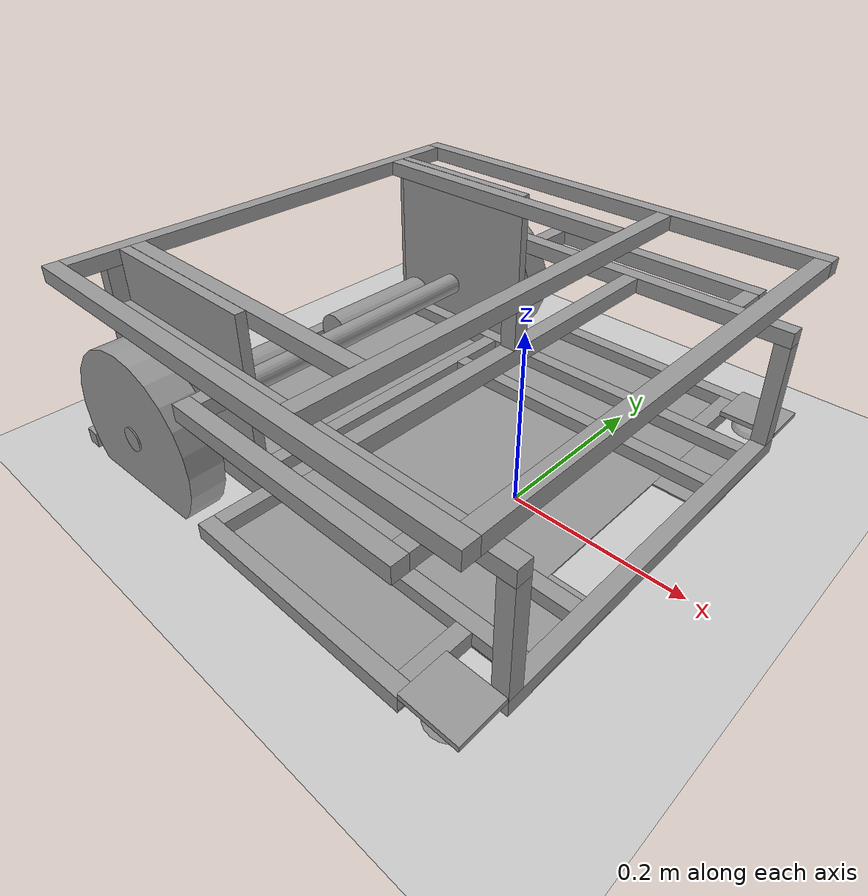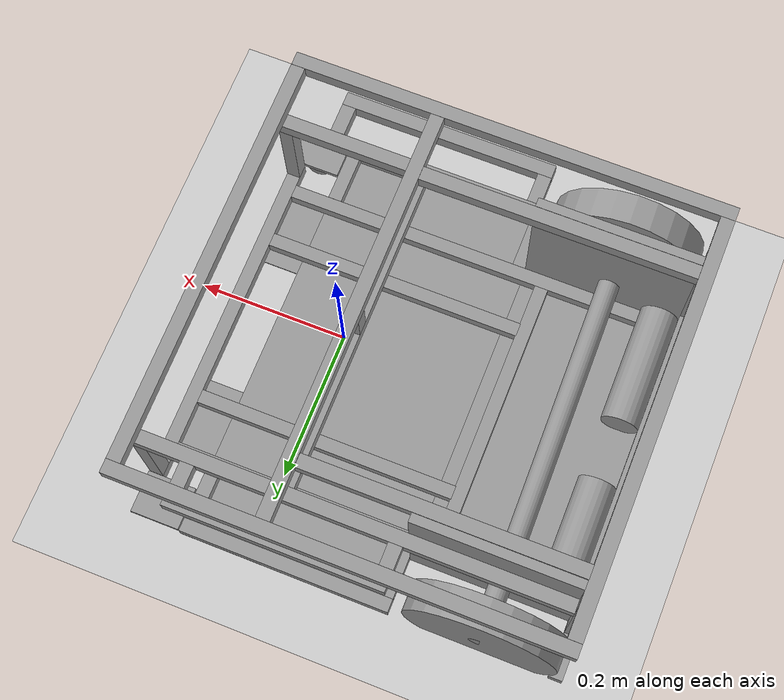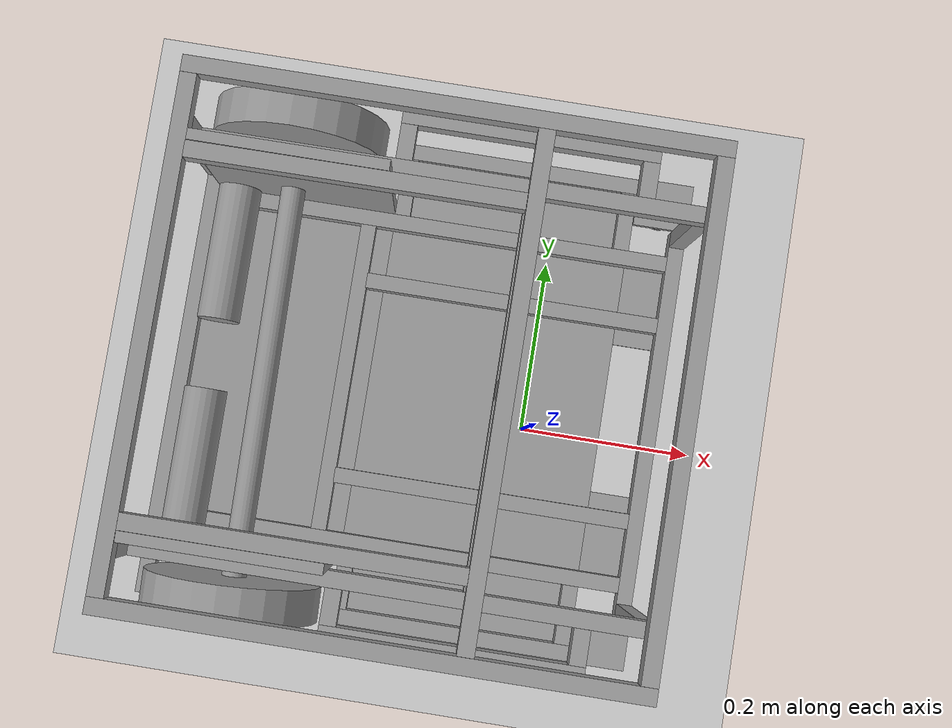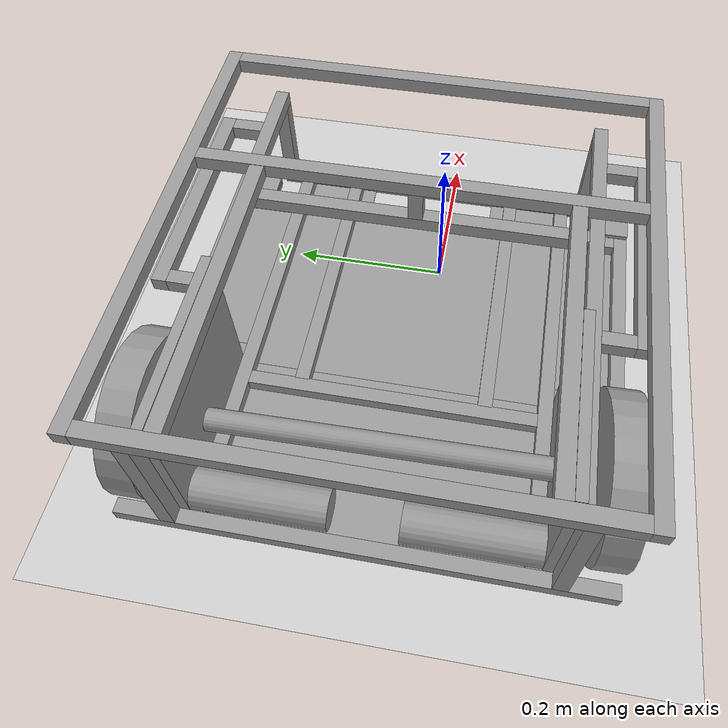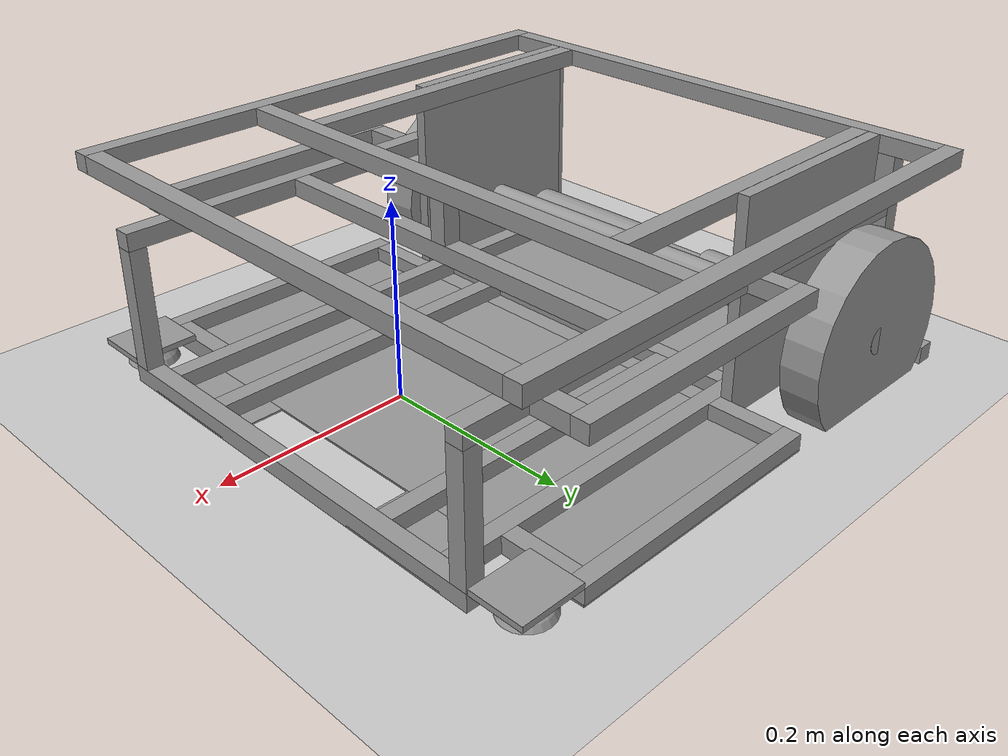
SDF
<?xml version="1.0"?>
<sdf version="1.4">
<world name="default">
<!-- Ground Plane -->
<include>
<uri>model://ground_plane</uri>
</include>
<include>
<uri>model://sun</uri>
</include>

  <model name='Modello_Robot_Completo'>
    <link name='link_1'>
      <pose frame=''>-0.048122 0.028866 0 0 -0 0</pose>
      <inertial>
        <mass>0.8771</mass>
        <inertia>
          <ixx>0.166667</ixx>
          <ixy>0</ixy>
          <ixz>0</ixz>
          <iyy>0.166667</iyy>
          <iyz>0</iyz>
          <izz>0.166667</izz>
        </inertia>
        <pose frame=''>0 0 0 0 -0 0</pose>
      </inertial>
      <self_collide>0</self_collide>
      <kinematic>0</kinematic>
      <visual name='visual'>
        <pose frame=''>0 0 0 0 -0 0</pose>
        <geometry>
          <box>
            <size>0.282 0.576 0.002</size>
          </box>
        </geometry>
        <material>
          <lighting>1</lighting>
          <script>
            <uri>file://media/materials/scripts/gazebo.material</uri>
            <name>Gazebo/Grey</name>
          </script>
          <ambient>0.3 0.3 0.3 1</ambient>
          <diffuse>0.7 0.7 0.7 1</diffuse>
          <specular>0.01 0.01 0.01 1</specular>
          <emissive>0 0 0 1</emissive>
          <shader type='vertex'>
            <normal_map>__default__</normal_map>
          </shader>
        </material>
        <cast_shadows>1</cast_shadows>
        <transparency>0</transparency>
      </visual>
      <collision name='collision'>
        <laser_retro>0</laser_retro>
        <max_contacts>10</max_contacts>
        <pose frame=''>0 0 0 0 -0 0</pose>
        <geometry>
          <box>
            <size>0.282 0.576 0.002</size>
          </box>
        </geometry>
        <surface>
          <friction>
            <ode>
              <mu>1</mu>
              <mu2>1</mu2>
              <fdir1>0 0 0</fdir1>
              <slip1>0</slip1>
              <slip2>0</slip2>
            </ode>
            <torsional>
              <coefficient>1</coefficient>
              <patch_radius>0</patch_radius>
              <surface_radius>0</surface_radius>
              <use_patch_radius>1</use_patch_radius>
              <ode>
                <slip>0</slip>
              </ode>
            </torsional>
          </friction>
          <bounce>
            <restitution_coefficient>0</restitution_coefficient>
            <threshold>1e+06</threshold>
          </bounce>
          <contact>
            <collide_without_contact>0</collide_without_contact>
            <collide_without_contact_bitmask>1</collide_without_contact_bitmask>
            <collide_bitmask>1</collide_bitmask>
            <ode>
              <soft_cfm>0</soft_cfm>
              <soft_erp>0.2</soft_erp>
              <kp>1e+13</kp>
              <kd>1</kd>
              <max_vel>0.01</max_vel>
              <min_depth>0</min_depth>
            </ode>
            <bullet>
              <split_impulse>1</split_impulse>
              <split_impulse_penetration_threshold>-0.01</split_impulse_penetration_threshold>
              <soft_cfm>0</soft_cfm>
              <soft_erp>0.2</soft_erp>
              <kp>1e+13</kp>
              <kd>1</kd>
            </bullet>
          </contact>
        </surface>
      </collision>
    </link>
    <link name='link_0'>
      <pose frame=''>-0.048122 0.307866 0.007996 -5e-06 8e-06 0</pose>
      <inertial>
        <mass>0.13</mass>
        <inertia>
          <ixx>0.166667</ixx>
          <ixy>0</ixy>
          <ixz>0</ixz>
          <iyy>0.166667</iyy>
          <iyz>0</iyz>
          <izz>0.166667</izz>
        </inertia>
        <pose frame=''>0 0 0 0 -0 0</pose>
      </inertial>
      <self_collide>0</self_collide>
      <kinematic>0</kinematic>
      <visual name='visual'>
        <pose frame=''>0 0 0 0 -0 0</pose>
        <geometry>
          <box>
            <size>0.282 0.018 0.018</size>
          </box>
        </geometry>
        <material>
          <lighting>1</lighting>
          <script>
            <uri>file://media/materials/scripts/gazebo.material</uri>
            <name>Gazebo/Grey</name>
          </script>
          <ambient>0.3 0.3 0.3 1</ambient>
          <diffuse>0.7 0.7 0.7 1</diffuse>
          <specular>0.01 0.01 0.01 1</specular>
          <emissive>0 0 0 1</emissive>
          <shader type='vertex'>
            <normal_map>__default__</normal_map>
          </shader>
        </material>
        <cast_shadows>1</cast_shadows>
        <transparency>0</transparency>
      </visual>
      <collision name='collision'>
        <laser_retro>0</laser_retro>
        <max_contacts>10</max_contacts>
        <pose frame=''>0 0 0 0 -0 0</pose>
        <geometry>
          <box>
            <size>0.282 0.018 0.018</size>
          </box>
        </geometry>
        <surface>
          <friction>
            <ode>
              <mu>1</mu>
              <mu2>1</mu2>
              <fdir1>0 0 0</fdir1>
              <slip1>0</slip1>
              <slip2>0</slip2>
            </ode>
            <torsional>
              <coefficient>1</coefficient>
              <patch_radius>0</patch_radius>
              <surface_radius>0</surface_radius>
              <use_patch_radius>1</use_patch_radius>
              <ode>
                <slip>0</slip>
              </ode>
            </torsional>
          </friction>
          <bounce>
            <restitution_coefficient>0</restitution_coefficient>
            <threshold>1e+06</threshold>
          </bounce>
          <contact>
            <collide_without_contact>0</collide_without_contact>
            <collide_without_contact_bitmask>1</collide_without_contact_bitmask>
            <collide_bitmask>1</collide_bitmask>
            <ode>
              <soft_cfm>0</soft_cfm>
              <soft_erp>0.2</soft_erp>
              <kp>1e+13</kp>
              <kd>1</kd>
              <max_vel>0.01</max_vel>
              <min_depth>0</min_depth>
            </ode>
            <bullet>
              <split_impulse>1</split_impulse>
              <split_impulse_penetration_threshold>-0.01</split_impulse_penetration_threshold>
              <soft_cfm>0</soft_cfm>
              <soft_erp>0.2</soft_erp>
              <kp>1e+13</kp>
              <kd>1</kd>
            </bullet>
          </contact>
        </surface>
      </collision>
    </link>
    <link name='link_0_0'>
      <pose frame=''>-0.130122 -0.163133 0.007999 -7e-06 4e-06 1.3e-05</pose>
      <inertial>
        <mass>0.277</mass>
        <inertia>
          <ixx>0.166667</ixx>
          <ixy>0</ixy>
          <ixz>0</ixz>
          <iyy>0.166667</iyy>
          <iyz>0</iyz>
          <izz>0.166667</izz>
        </inertia>
        <pose frame=''>0 0 0 0 -0 0</pose>
      </inertial>
      <self_collide>0</self_collide>
      <kinematic>0</kinematic>
      <visual name='visual'>
        <pose frame=''>0 0 0 0 -0 0</pose>
        <geometry>
          <box>
            <size>0.54 0.018 0.018</size>
          </box>
        </geometry>
        <material>
          <lighting>1</lighting>
          <script>
            <uri>file://media/materials/scripts/gazebo.material</uri>
            <name>Gazebo/Grey</name>
          </script>
          <ambient>0.3 0.3 0.3 1</ambient>
          <diffuse>0.7 0.7 0.7 1</diffuse>
          <specular>0.01 0.01 0.01 1</specular>
          <emissive>0 0 0 1</emissive>
          <shader type='vertex'>
            <normal_map>__default__</normal_map>
          </shader>
        </material>
        <cast_shadows>1</cast_shadows>
        <transparency>0</transparency>
      </visual>
      <collision name='collision'>
        <laser_retro>0</laser_retro>
        <max_contacts>10</max_contacts>
        <pose frame=''>0 0 0 0 -0 0</pose>
        <geometry>
          <box>
            <size>0.54 0.018 0.018</size>
          </box>
        </geometry>
        <surface>
          <friction>
            <ode>
              <mu>1</mu>
              <mu2>1</mu2>
              <fdir1>0 0 0</fdir1>
              <slip1>0</slip1>
              <slip2>0</slip2>
            </ode>
            <torsional>
              <coefficient>1</coefficient>
              <patch_radius>0</patch_radius>
              <surface_radius>0</surface_radius>
              <use_patch_radius>1</use_patch_radius>
              <ode>
                <slip>0</slip>
              </ode>
            </torsional>
          </friction>
          <bounce>
            <restitution_coefficient>0</restitution_coefficient>
            <threshold>1e+06</threshold>
          </bounce>
          <contact>
            <collide_without_contact>0</collide_without_contact>
            <collide_without_contact_bitmask>1</collide_without_contact_bitmask>
            <collide_bitmask>1</collide_bitmask>
            <ode>
              <soft_cfm>0</soft_cfm>
              <soft_erp>0.2</soft_erp>
              <kp>1e+13</kp>
              <kd>1</kd>
              <max_vel>0.01</max_vel>
              <min_depth>0</min_depth>
            </ode>
            <bullet>
              <split_impulse>1</split_impulse>
              <split_impulse_penetration_threshold>-0.01</split_impulse_penetration_threshold>
              <soft_cfm>0</soft_cfm>
              <soft_erp>0.2</soft_erp>
              <kp>1e+13</kp>
              <kd>1</kd>
            </bullet>
          </contact>
        </surface>
      </collision>
    </link>
    <link name='link_0_0_clone'>
      <pose frame=''>-0.130127 0.220866 0.007997 -1.4e-05 8e-06 2.6e-05</pose>
      <inertial>
        <mass>0.277</mass>
        <inertia>
          <ixx>0.166667</ixx>
          <ixy>0</ixy>
          <ixz>0</ixz>
          <iyy>0.166667</iyy>
          <iyz>0</iyz>
          <izz>0.166667</izz>
        </inertia>
        <pose frame=''>0 0 0 0 -0 0</pose>
      </inertial>
      <self_collide>0</self_collide>
      <kinematic>0</kinematic>
      <visual name='visual_0'>
        <pose frame=''>0 0 0 0 -0 0</pose>
        <geometry>
          <box>
            <size>0.54 0.018 0.018</size>
          </box>
        </geometry>
        <material>
          <lighting>1</lighting>
          <script>
            <uri>file://media/materials/scripts/gazebo.material</uri>
            <name>Gazebo/Grey</name>
          </script>
          <ambient>0.3 0.3 0.3 1</ambient>
          <diffuse>0.7 0.7 0.7 1</diffuse>
          <specular>0.01 0.01 0.01 1</specular>
          <emissive>0 0 0 1</emissive>
          <shader type='vertex'>
            <normal_map>__default__</normal_map>
          </shader>
        </material>
        <cast_shadows>1</cast_shadows>
        <transparency>0</transparency>
      </visual>
      <collision name='collision'>
        <laser_retro>0</laser_retro>
        <max_contacts>10</max_contacts>
        <pose frame=''>0 0 0 0 -0 0</pose>
        <geometry>
          <box>
            <size>0.54 0.018 0.018</size>
          </box>
        </geometry>
        <surface>
          <friction>
            <ode>
              <mu>1</mu>
              <mu2>1</mu2>
              <fdir1>0 0 0</fdir1>
              <slip1>0</slip1>
              <slip2>0</slip2>
            </ode>
            <torsional>
              <coefficient>1</coefficient>
              <patch_radius>0</patch_radius>
              <surface_radius>0</surface_radius>
              <use_patch_radius>1</use_patch_radius>
              <ode>
                <slip>0</slip>
              </ode>
            </torsional>
          </friction>
          <bounce>
            <restitution_coefficient>0</restitution_coefficient>
            <threshold>1e+06</threshold>
          </bounce>
          <contact>
            <collide_without_contact>0</collide_without_contact>
            <collide_without_contact_bitmask>1</collide_without_contact_bitmask>
            <collide_bitmask>1</collide_bitmask>
            <ode>
              <soft_cfm>0</soft_cfm>
              <soft_erp>0.2</soft_erp>
              <kp>1e+13</kp>
              <kd>1</kd>
              <max_vel>0.01</max_vel>
              <min_depth>0</min_depth>
            </ode>
            <bullet>
              <split_impulse>1</split_impulse>
              <split_impulse_penetration_threshold>-0.01</split_impulse_penetration_threshold>
              <soft_cfm>0</soft_cfm>
              <soft_erp>0.2</soft_erp>
              <kp>1e+13</kp>
              <kd>1</kd>
            </bullet>
          </contact>
        </surface>
      </collision>
    </link>
    <link name='link_0_1'>
      <pose frame=''>-0.035122 -0.088134 0.008001 -6e-06 5e-06 -3e-06</pose>
      <inertial>
        <mass>0.183</mass>
        <inertia>
          <ixx>0.166667</ixx>
          <ixy>0</ixy>
          <ixz>0</ixz>
          <iyy>0.166667</iyy>
          <iyz>0</iyz>
          <izz>0.166667</izz>
        </inertia>
        <pose frame=''>0 0 0 0 -0 0</pose>
      </inertial>
      <self_collide>0</self_collide>
      <kinematic>0</kinematic>
      <visual name='visual'>
        <pose frame=''>0 0 0 0 -0 0</pose>
        <geometry>
          <box>
            <size>0.35 0.018 0.018</size>
          </box>
        </geometry>
        <material>
          <lighting>1</lighting>
          <script>
            <uri>file://media/materials/scripts/gazebo.material</uri>
            <name>Gazebo/Grey</name>
          </script>
          <ambient>0.3 0.3 0.3 1</ambient>
          <diffuse>0.7 0.7 0.7 1</diffuse>
          <specular>0.01 0.01 0.01 1</specular>
          <emissive>0 0 0 1</emissive>
          <shader type='vertex'>
            <normal_map>__default__</normal_map>
          </shader>
        </material>
        <cast_shadows>1</cast_shadows>
        <transparency>0</transparency>
      </visual>
      <collision name='collision'>
        <laser_retro>0</laser_retro>
        <max_contacts>10</max_contacts>
        <pose frame=''>0 0 0 0 -0 0</pose>
        <geometry>
          <box>
            <size>0.35 0.018 0.018</size>
          </box>
        </geometry>
        <surface>
          <friction>
            <ode>
              <mu>1</mu>
              <mu2>1</mu2>
              <fdir1>0 0 0</fdir1>
              <slip1>0</slip1>
              <slip2>0</slip2>
            </ode>
            <torsional>
              <coefficient>1</coefficient>
              <patch_radius>0</patch_radius>
              <surface_radius>0</surface_radius>
              <use_patch_radius>1</use_patch_radius>
              <ode>
                <slip>0</slip>
              </ode>
            </torsional>
          </friction>
          <bounce>
            <restitution_coefficient>0</restitution_coefficient>
            <threshold>1e+06</threshold>
          </bounce>
          <contact>
            <collide_without_contact>0</collide_without_contact>
            <collide_without_contact_bitmask>1</collide_without_contact_bitmask>
            <collide_bitmask>1</collide_bitmask>
            <ode>
              <soft_cfm>0</soft_cfm>
              <soft_erp>0.2</soft_erp>
              <kp>1e+13</kp>
              <kd>1</kd>
              <max_vel>0.01</max_vel>
              <min_depth>0</min_depth>
            </ode>
            <bullet>
              <split_impulse>1</split_impulse>
              <split_impulse_penetration_threshold>-0.01</split_impulse_penetration_threshold>
              <soft_cfm>0</soft_cfm>
              <soft_erp>0.2</soft_erp>
              <kp>1e+13</kp>
              <kd>1</kd>
            </bullet>
          </contact>
        </surface>
      </collision>
    </link>
    <link name='link_0_1_clone'>
      <pose frame=''>-0.035122 0.145866 0.008001 -1.2e-05 1e-05 -6e-06</pose>
      <inertial>
        <mass>0.183</mass>
        <inertia>
          <ixx>0.166667</ixx>
          <ixy>0</ixy>
          <ixz>0</ixz>
          <iyy>0.166667</iyy>
          <iyz>0</iyz>
          <izz>0.166667</izz>
        </inertia>
        <pose frame=''>0 0 0 0 -0 0</pose>
      </inertial>
      <self_collide>0</self_collide>
      <kinematic>0</kinematic>
      <visual name='visual_0'>
        <pose frame=''>0 0 0 0 -0 0</pose>
        <geometry>
          <box>
            <size>0.35 0.018 0.018</size>
          </box>
        </geometry>
        <material>
          <lighting>1</lighting>
          <script>
            <uri>file://media/materials/scripts/gazebo.material</uri>
            <name>Gazebo/Grey</name>
          </script>
          <ambient>0.3 0.3 0.3 1</ambient>
          <diffuse>0.7 0.7 0.7 1</diffuse>
          <specular>0.01 0.01 0.01 1</specular>
          <emissive>0 0 0 1</emissive>
          <shader type='vertex'>
            <normal_map>__default__</normal_map>
          </shader>
        </material>
        <cast_shadows>1</cast_shadows>
        <transparency>0</transparency>
      </visual>
      <collision name='collision'>
        <laser_retro>0</laser_retro>
        <max_contacts>10</max_contacts>
        <pose frame=''>0 0 0 0 -0 0</pose>
        <geometry>
          <box>
            <size>0.35 0.018 0.018</size>
          </box>
        </geometry>
        <surface>
          <friction>
            <ode>
              <mu>1</mu>
              <mu2>1</mu2>
              <fdir1>0 0 0</fdir1>
              <slip1>0</slip1>
              <slip2>0</slip2>
            </ode>
            <torsional>
              <coefficient>1</coefficient>
              <patch_radius>0</patch_radius>
              <surface_radius>0</surface_radius>
              <use_patch_radius>1</use_patch_radius>
              <ode>
                <slip>0</slip>
              </ode>
            </torsional>
          </friction>
          <bounce>
            <restitution_coefficient>0</restitution_coefficient>
            <threshold>1e+06</threshold>
          </bounce>
          <contact>
            <collide_without_contact>0</collide_without_contact>
            <collide_without_contact_bitmask>1</collide_without_contact_bitmask>
            <collide_bitmask>1</collide_bitmask>
            <ode>
              <soft_cfm>0</soft_cfm>
              <soft_erp>0.2</soft_erp>
              <kp>1e+13</kp>
              <kd>1</kd>
              <max_vel>0.01</max_vel>
              <min_depth>0</min_depth>
            </ode>
            <bullet>
              <split_impulse>1</split_impulse>
              <split_impulse_penetration_threshold>-0.01</split_impulse_penetration_threshold>
              <soft_cfm>0</soft_cfm>
              <soft_erp>0.2</soft_erp>
              <kp>1e+13</kp>
              <kd>1</kd>
            </bullet>
          </contact>
        </surface>
      </collision>
    </link>
    <link name='link_0_2'>
      <pose frame=''>0.083879 -0.206635 0.007998 -5e-06 6e-06 -4e-06</pose>
      <inertial>
        <mass>0.037</mass>
        <inertia>
          <ixx>0.166667</ixx>
          <ixy>0</ixy>
          <ixz>0</ixz>
          <iyy>0.166667</iyy>
          <iyz>0</iyz>
          <izz>0.166667</izz>
        </inertia>
        <pose frame=''>0 0 0 0 -0 0</pose>
      </inertial>
      <self_collide>0</self_collide>
      <kinematic>0</kinematic>
      <visual name='visual'>
        <pose frame=''>0 0 0 0 -0 0</pose>
        <geometry>
          <box>
            <size>0.018 0.069 0.018</size>
          </box>
        </geometry>
        <material>
          <lighting>1</lighting>
          <script>
            <uri>file://media/materials/scripts/gazebo.material</uri>
            <name>Gazebo/Grey</name>
          </script>
          <ambient>0.3 0.3 0.3 1</ambient>
          <diffuse>0.7 0.7 0.7 1</diffuse>
          <specular>0.01 0.01 0.01 1</specular>
          <emissive>0 0 0 1</emissive>
          <shader type='vertex'>
            <normal_map>__default__</normal_map>
          </shader>
        </material>
        <cast_shadows>1</cast_shadows>
        <transparency>0</transparency>
      </visual>
      <collision name='collision'>
        <laser_retro>0</laser_retro>
        <max_contacts>10</max_contacts>
        <pose frame=''>0 0 0 0 -0 0</pose>
        <geometry>
          <box>
            <size>0.018 0.069 0.018</size>
          </box>
        </geometry>
        <surface>
          <friction>
            <ode>
              <mu>1</mu>
              <mu2>1</mu2>
              <fdir1>0 0 0</fdir1>
              <slip1>0</slip1>
              <slip2>0</slip2>
            </ode>
            <torsional>
              <coefficient>1</coefficient>
              <patch_radius>0</patch_radius>
              <surface_radius>0</surface_radius>
              <use_patch_radius>1</use_patch_radius>
              <ode>
                <slip>0</slip>
              </ode>
            </torsional>
          </friction>
          <bounce>
            <restitution_coefficient>0</restitution_coefficient>
            <threshold>1e+06</threshold>
          </bounce>
          <contact>
            <collide_without_contact>0</collide_without_contact>
            <collide_without_contact_bitmask>1</collide_without_contact_bitmask>
            <collide_bitmask>1</collide_bitmask>
            <ode>
              <soft_cfm>0</soft_cfm>
              <soft_erp>0.2</soft_erp>
              <kp>1e+13</kp>
              <kd>1</kd>
              <max_vel>0.01</max_vel>
              <min_depth>0</min_depth>
            </ode>
            <bullet>
              <split_impulse>1</split_impulse>
              <split_impulse_penetration_threshold>-0.01</split_impulse_penetration_threshold>
              <soft_cfm>0</soft_cfm>
              <soft_erp>0.2</soft_erp>
              <kp>1e+13</kp>
              <kd>1</kd>
            </bullet>
          </contact>
        </surface>
      </collision>
    </link>
    <link name='link_0_2_clone'>
      <pose frame=''>-0.180124 -0.206634 0.008 -1e-05 1.2e-05 -8e-06</pose>
      <inertial>
        <mass>0.037</mass>
        <inertia>
          <ixx>0.166667</ixx>
          <ixy>0</ixy>
          <ixz>0</ixz>
          <iyy>0.166667</iyy>
          <iyz>0</iyz>
          <izz>0.166667</izz>
        </inertia>
        <pose frame=''>0 0 0 0 -0 0</pose>
      </inertial>
      <self_collide>0</self_collide>
      <kinematic>0</kinematic>
      <visual name='visual_0'>
        <pose frame=''>0 0 0 0 -0 0</pose>
        <geometry>
          <box>
            <size>0.018 0.069 0.018</size>
          </box>
        </geometry>
        <material>
          <lighting>1</lighting>
          <script>
            <uri>file://media/materials/scripts/gazebo.material</uri>
            <name>Gazebo/Grey</name>
          </script>
          <ambient>0.3 0.3 0.3 1</ambient>
          <diffuse>0.7 0.7 0.7 1</diffuse>
          <specular>0.01 0.01 0.01 1</specular>
          <emissive>0 0 0 1</emissive>
          <shader type='vertex'>
            <normal_map>__default__</normal_map>
          </shader>
        </material>
        <cast_shadows>1</cast_shadows>
        <transparency>0</transparency>
      </visual>
      <collision name='collision'>
        <laser_retro>0</laser_retro>
        <max_contacts>10</max_contacts>
        <pose frame=''>0 0 0 0 -0 0</pose>
        <geometry>
          <box>
            <size>0.018 0.069 0.018</size>
          </box>
        </geometry>
        <surface>
          <friction>
            <ode>
              <mu>1</mu>
              <mu2>1</mu2>
              <fdir1>0 0 0</fdir1>
              <slip1>0</slip1>
              <slip2>0</slip2>
            </ode>
            <torsional>
              <coefficient>1</coefficient>
              <patch_radius>0</patch_radius>
              <surface_radius>0</surface_radius>
              <use_patch_radius>1</use_patch_radius>
              <ode>
                <slip>0</slip>
              </ode>
            </torsional>
          </friction>
          <bounce>
            <restitution_coefficient>0</restitution_coefficient>
            <threshold>1e+06</threshold>
          </bounce>
          <contact>
            <collide_without_contact>0</collide_without_contact>
            <collide_without_contact_bitmask>1</collide_without_contact_bitmask>
            <collide_bitmask>1</collide_bitmask>
            <ode>
              <soft_cfm>0</soft_cfm>
              <soft_erp>0.2</soft_erp>
              <kp>1e+13</kp>
              <kd>1</kd>
              <max_vel>0.01</max_vel>
              <min_depth>0</min_depth>
            </ode>
            <bullet>
              <split_impulse>1</split_impulse>
              <split_impulse_penetration_threshold>-0.01</split_impulse_penetration_threshold>
              <soft_cfm>0</soft_cfm>
              <soft_erp>0.2</soft_erp>
              <kp>1e+13</kp>
              <kd>1</kd>
            </bullet>
          </contact>
        </surface>
      </collision>
    </link>
    <link name='link_0_2_clone_0'>
      <pose frame=''>0.083879 0.264366 0.007996 -1e-05 1.2e-05 -8e-06</pose>
      <inertial>
        <mass>0.037</mass>
        <inertia>
          <ixx>0.166667</ixx>
          <ixy>0</ixy>
          <ixz>0</ixz>
          <iyy>0.166667</iyy>
          <iyz>0</iyz>
          <izz>0.166667</izz>
        </inertia>
        <pose frame=''>0 0 0 0 -0 0</pose>
      </inertial>
      <self_collide>0</self_collide>
      <kinematic>0</kinematic>
      <visual name='visual_0'>
        <pose frame=''>0 0 0 0 -0 0</pose>
        <geometry>
          <box>
            <size>0.018 0.069 0.018</size>
          </box>
        </geometry>
        <material>
          <lighting>1</lighting>
          <script>
            <uri>file://media/materials/scripts/gazebo.material</uri>
            <name>Gazebo/Grey</name>
          </script>
          <ambient>0.3 0.3 0.3 1</ambient>
          <diffuse>0.7 0.7 0.7 1</diffuse>
          <specular>0.01 0.01 0.01 1</specular>
          <emissive>0 0 0 1</emissive>
          <shader type='vertex'>
            <normal_map>__default__</normal_map>
          </shader>
        </material>
        <cast_shadows>1</cast_shadows>
        <transparency>0</transparency>
      </visual>
      <collision name='collision'>
        <laser_retro>0</laser_retro>
        <max_contacts>10</max_contacts>
        <pose frame=''>0 0 0 0 -0 0</pose>
        <geometry>
          <box>
            <size>0.018 0.069 0.018</size>
          </box>
        </geometry>
        <surface>
          <friction>
            <ode>
              <mu>1</mu>
              <mu2>1</mu2>
              <fdir1>0 0 0</fdir1>
              <slip1>0</slip1>
              <slip2>0</slip2>
            </ode>
            <torsional>
              <coefficient>1</coefficient>
              <patch_radius>0</patch_radius>
              <surface_radius>0</surface_radius>
              <use_patch_radius>1</use_patch_radius>
              <ode>
                <slip>0</slip>
              </ode>
            </torsional>
          </friction>
          <bounce>
            <restitution_coefficient>0</restitution_coefficient>
            <threshold>1e+06</threshold>
          </bounce>
          <contact>
            <collide_without_contact>0</collide_without_contact>
            <collide_without_contact_bitmask>1</collide_without_contact_bitmask>
            <collide_bitmask>1</collide_bitmask>
            <ode>
              <soft_cfm>0</soft_cfm>
              <soft_erp>0.2</soft_erp>
              <kp>1e+13</kp>
              <kd>1</kd>
              <max_vel>0.01</max_vel>
              <min_depth>0</min_depth>
            </ode>
            <bullet>
              <split_impulse>1</split_impulse>
              <split_impulse_penetration_threshold>-0.01</split_impulse_penetration_threshold>
              <soft_cfm>0</soft_cfm>
              <soft_erp>0.2</soft_erp>
              <kp>1e+13</kp>
              <kd>1</kd>
            </bullet>
          </contact>
        </surface>
      </collision>
    </link>
    <link name='link_0_2_clone_1'>
      <pose frame=''>-0.180122 0.264367 0.007997 -1e-05 1.2e-05 -8e-06</pose>
      <inertial>
        <mass>0.037</mass>
        <inertia>
          <ixx>0.166667</ixx>
          <ixy>0</ixy>
          <ixz>0</ixz>
          <iyy>0.166667</iyy>
          <iyz>0</iyz>
          <izz>0.166667</izz>
        </inertia>
        <pose frame=''>0 0 0 0 -0 0</pose>
      </inertial>
      <self_collide>0</self_collide>
      <kinematic>0</kinematic>
      <visual name='visual_0'>
        <pose frame=''>0 0 0 0 -0 0</pose>
        <geometry>
          <box>
            <size>0.018 0.069 0.018</size>
          </box>
        </geometry>
        <material>
          <lighting>1</lighting>
          <script>
            <uri>file://media/materials/scripts/gazebo.material</uri>
            <name>Gazebo/Grey</name>
          </script>
          <ambient>0.3 0.3 0.3 1</ambient>
          <diffuse>0.7 0.7 0.7 1</diffuse>
          <specular>0.01 0.01 0.01 1</specular>
          <emissive>0 0 0 1</emissive>
          <shader type='vertex'>
            <normal_map>__default__</normal_map>
          </shader>
        </material>
        <cast_shadows>1</cast_shadows>
        <transparency>0</transparency>
      </visual>
      <collision name='collision'>
        <laser_retro>0</laser_retro>
        <max_contacts>10</max_contacts>
        <pose frame=''>0 0 0 0 -0 0</pose>
        <geometry>
          <box>
            <size>0.018 0.069 0.018</size>
          </box>
        </geometry>
        <surface>
          <friction>
            <ode>
              <mu>1</mu>
              <mu2>1</mu2>
              <fdir1>0 0 0</fdir1>
              <slip1>0</slip1>
              <slip2>0</slip2>
            </ode>
            <torsional>
              <coefficient>1</coefficient>
              <patch_radius>0</patch_radius>
              <surface_radius>0</surface_radius>
              <use_patch_radius>1</use_patch_radius>
              <ode>
                <slip>0</slip>
              </ode>
            </torsional>
          </friction>
          <bounce>
            <restitution_coefficient>0</restitution_coefficient>
            <threshold>1e+06</threshold>
          </bounce>
          <contact>
            <collide_without_contact>0</collide_without_contact>
            <collide_without_contact_bitmask>1</collide_without_contact_bitmask>
            <collide_bitmask>1</collide_bitmask>
            <ode>
              <soft_cfm>0</soft_cfm>
              <soft_erp>0.2</soft_erp>
              <kp>1e+13</kp>
              <kd>1</kd>
              <max_vel>0.01</max_vel>
              <min_depth>0</min_depth>
            </ode>
            <bullet>
              <split_impulse>1</split_impulse>
              <split_impulse_penetration_threshold>-0.01</split_impulse_penetration_threshold>
              <soft_cfm>0</soft_cfm>
              <soft_erp>0.2</soft_erp>
              <kp>1e+13</kp>
              <kd>1</kd>
            </bullet>
          </contact>
        </surface>
      </collision>
    </link>
    <link name='link_0_3'>
      <pose frame=''>0.148879 -0.193134 0.079497 -5e-06 8e-06 1e-05</pose>
      <inertial>
        <mass>0.062</mass>
        <inertia>
          <ixx>0.166667</ixx>
          <ixy>0</ixy>
          <ixz>0</ixz>
          <iyy>0.166667</iyy>
          <iyz>0</iyz>
          <izz>0.166667</izz>
        </inertia>
        <pose frame=''>0 0 0 0 -0 0</pose>
      </inertial>
      <self_collide>0</self_collide>
      <kinematic>0</kinematic>
      <visual name='visual'>
        <pose frame=''>0 0 0 0 -0 0</pose>
        <geometry>
          <box>
            <size>0.018 0.018 0.125</size>
          </box>
        </geometry>
        <material>
          <lighting>1</lighting>
          <script>
            <uri>file://media/materials/scripts/gazebo.material</uri>
            <name>Gazebo/Grey</name>
          </script>
          <ambient>0.3 0.3 0.3 1</ambient>
          <diffuse>0.7 0.7 0.7 1</diffuse>
          <specular>0.01 0.01 0.01 1</specular>
          <emissive>0 0 0 1</emissive>
          <shader type='vertex'>
            <normal_map>__default__</normal_map>
          </shader>
        </material>
        <cast_shadows>1</cast_shadows>
        <transparency>0</transparency>
      </visual>
      <collision name='collision'>
        <laser_retro>0</laser_retro>
        <max_contacts>10</max_contacts>
        <pose frame=''>0 0 0 0 -0 0</pose>
        <geometry>
          <box>
            <size>0.018 0.018 0.125</size>
          </box>
        </geometry>
        <surface>
          <friction>
            <ode>
              <mu>1</mu>
              <mu2>1</mu2>
              <fdir1>0 0 0</fdir1>
              <slip1>0</slip1>
              <slip2>0</slip2>
            </ode>
            <torsional>
              <coefficient>1</coefficient>
              <patch_radius>0</patch_radius>
              <surface_radius>0</surface_radius>
              <use_patch_radius>1</use_patch_radius>
              <ode>
                <slip>0</slip>
              </ode>
            </torsional>
          </friction>
          <bounce>
            <restitution_coefficient>0</restitution_coefficient>
            <threshold>1e+06</threshold>
          </bounce>
          <contact>
            <collide_without_contact>0</collide_without_contact>
            <collide_without_contact_bitmask>1</collide_without_contact_bitmask>
            <collide_bitmask>1</collide_bitmask>
            <ode>
              <soft_cfm>0</soft_cfm>
              <soft_erp>0.2</soft_erp>
              <kp>1e+13</kp>
              <kd>1</kd>
              <max_vel>0.01</max_vel>
              <min_depth>0</min_depth>
            </ode>
            <bullet>
              <split_impulse>1</split_impulse>
              <split_impulse_penetration_threshold>-0.01</split_impulse_penetration_threshold>
              <soft_cfm>0</soft_cfm>
              <soft_erp>0.2</soft_erp>
              <kp>1e+13</kp>
              <kd>1</kd>
            </bullet>
          </contact>
        </surface>
      </collision>
    </link>
    <link name='link_0_3_clone'>
      <pose frame=''>0.148875 0.250866 0.079495 -1e-05 1.6e-05 2e-05</pose>
      <inertial>
        <mass>0.062</mass>
        <inertia>
          <ixx>0.166667</ixx>
          <ixy>0</ixy>
          <ixz>0</ixz>
          <iyy>0.166667</iyy>
          <iyz>0</iyz>
          <izz>0.166667</izz>
        </inertia>
        <pose frame=''>0 0 0 0 -0 0</pose>
      </inertial>
      <self_collide>0</self_collide>
      <kinematic>0</kinematic>
      <visual name='visual_0'>
        <pose frame=''>0 0 0 0 -0 0</pose>
        <geometry>
          <box>
            <size>0.018 0.018 0.125</size>
          </box>
        </geometry>
        <material>
          <lighting>1</lighting>
          <script>
            <uri>file://media/materials/scripts/gazebo.material</uri>
            <name>Gazebo/Grey</name>
          </script>
          <ambient>0.3 0.3 0.3 1</ambient>
          <diffuse>0.7 0.7 0.7 1</diffuse>
          <specular>0.01 0.01 0.01 1</specular>
          <emissive>0 0 0 1</emissive>
          <shader type='vertex'>
            <normal_map>__default__</normal_map>
          </shader>
        </material>
        <cast_shadows>1</cast_shadows>
        <transparency>0</transparency>
      </visual>
      <collision name='collision'>
        <laser_retro>0</laser_retro>
        <max_contacts>10</max_contacts>
        <pose frame=''>0 0 0 0 -0 0</pose>
        <geometry>
          <box>
            <size>0.018 0.018 0.125</size>
          </box>
        </geometry>
        <surface>
          <friction>
            <ode>
              <mu>1</mu>
              <mu2>1</mu2>
              <fdir1>0 0 0</fdir1>
              <slip1>0</slip1>
              <slip2>0</slip2>
            </ode>
            <torsional>
              <coefficient>1</coefficient>
              <patch_radius>0</patch_radius>
              <surface_radius>0</surface_radius>
              <use_patch_radius>1</use_patch_radius>
              <ode>
                <slip>0</slip>
              </ode>
            </torsional>
          </friction>
          <bounce>
            <restitution_coefficient>0</restitution_coefficient>
            <threshold>1e+06</threshold>
          </bounce>
          <contact>
            <collide_without_contact>0</collide_without_contact>
            <collide_without_contact_bitmask>1</collide_without_contact_bitmask>
            <collide_bitmask>1</collide_bitmask>
            <ode>
              <soft_cfm>0</soft_cfm>
              <soft_erp>0.2</soft_erp>
              <kp>1e+13</kp>
              <kd>1</kd>
              <max_vel>0.01</max_vel>
              <min_depth>0</min_depth>
            </ode>
            <bullet>
              <split_impulse>1</split_impulse>
              <split_impulse_penetration_threshold>-0.01</split_impulse_penetration_threshold>
              <soft_cfm>0</soft_cfm>
              <soft_erp>0.2</soft_erp>
              <kp>1e+13</kp>
              <kd>1</kd>
            </bullet>
          </contact>
        </surface>
      </collision>
    </link>
    <link name='link_0_4'>
      <pose frame=''>-0.409144 -0.193135 0.1095 1e-06 -0 -5.5e-05</pose>
      <inertial>
        <mass>0.091</mass>
        <inertia>
          <ixx>0.166667</ixx>
          <ixy>0</ixy>
          <ixz>0</ixz>
          <iyy>0.166667</iyy>
          <iyz>0</iyz>
          <izz>0.166667</izz>
        </inertia>
        <pose frame=''>0 0 0 0 -0 0</pose>
      </inertial>
      <self_collide>0</self_collide>
      <kinematic>0</kinematic>
      <visual name='visual'>
        <pose frame=''>0 0 0 0 -0 0</pose>
        <geometry>
          <box>
            <size>0.018 0.018 0.185</size>
          </box>
        </geometry>
        <material>
          <lighting>1</lighting>
          <script>
            <uri>file://media/materials/scripts/gazebo.material</uri>
            <name>Gazebo/Grey</name>
          </script>
          <ambient>0.3 0.3 0.3 1</ambient>
          <diffuse>0.7 0.7 0.7 1</diffuse>
          <specular>0.01 0.01 0.01 1</specular>
          <emissive>0 0 0 1</emissive>
          <shader type='vertex'>
            <normal_map>__default__</normal_map>
          </shader>
        </material>
        <cast_shadows>1</cast_shadows>
        <transparency>0</transparency>
      </visual>
      <collision name='collision'>
        <laser_retro>0</laser_retro>
        <max_contacts>10</max_contacts>
        <pose frame=''>0 0 0 0 -0 0</pose>
        <geometry>
          <box>
            <size>0.018 0.018 0.185</size>
          </box>
        </geometry>
        <surface>
          <friction>
            <ode>
              <mu>1</mu>
              <mu2>1</mu2>
              <fdir1>0 0 0</fdir1>
              <slip1>0</slip1>
              <slip2>0</slip2>
            </ode>
            <torsional>
              <coefficient>1</coefficient>
              <patch_radius>0</patch_radius>
              <surface_radius>0</surface_radius>
              <use_patch_radius>1</use_patch_radius>
              <ode>
                <slip>0</slip>
              </ode>
            </torsional>
          </friction>
          <bounce>
            <restitution_coefficient>0</restitution_coefficient>
            <threshold>1e+06</threshold>
          </bounce>
          <contact>
            <collide_without_contact>0</collide_without_contact>
            <collide_without_contact_bitmask>1</collide_without_contact_bitmask>
            <collide_bitmask>1</collide_bitmask>
            <ode>
              <soft_cfm>0</soft_cfm>
              <soft_erp>0.2</soft_erp>
              <kp>1e+13</kp>
              <kd>1</kd>
              <max_vel>0.01</max_vel>
              <min_depth>0</min_depth>
            </ode>
            <bullet>
              <split_impulse>1</split_impulse>
              <split_impulse_penetration_threshold>-0.01</split_impulse_penetration_threshold>
              <soft_cfm>0</soft_cfm>
              <soft_erp>0.2</soft_erp>
              <kp>1e+13</kp>
              <kd>1</kd>
            </bullet>
          </contact>
        </surface>
      </collision>
    </link>
    <link name='link_0_4_clone'>
      <pose frame=''>-0.409122 0.250878 0.1095 2e-06 0 -0.00011</pose>
      <inertial>
        <mass>0.091</mass>
        <inertia>
          <ixx>0.166667</ixx>
          <ixy>0</ixy>
          <ixz>0</ixz>
          <iyy>0.166667</iyy>
          <iyz>0</iyz>
          <izz>0.166667</izz>
        </inertia>
        <pose frame=''>0 0 0 0 -0 0</pose>
      </inertial>
      <self_collide>0</self_collide>
      <kinematic>0</kinematic>
      <visual name='visual_0'>
        <pose frame=''>0 0 0 0 -0 0</pose>
        <geometry>
          <box>
            <size>0.018 0.018 0.185</size>
          </box>
        </geometry>
        <material>
          <lighting>1</lighting>
          <script>
            <uri>file://media/materials/scripts/gazebo.material</uri>
            <name>Gazebo/Grey</name>
          </script>
          <ambient>0.3 0.3 0.3 1</ambient>
          <diffuse>0.7 0.7 0.7 1</diffuse>
          <specular>0.01 0.01 0.01 1</specular>
          <emissive>0 0 0 1</emissive>
          <shader type='vertex'>
            <normal_map>__default__</normal_map>
          </shader>
        </material>
        <cast_shadows>1</cast_shadows>
        <transparency>0</transparency>
      </visual>
      <collision name='collision'>
        <laser_retro>0</laser_retro>
        <max_contacts>10</max_contacts>
        <pose frame=''>0 0 0 0 -0 0</pose>
        <geometry>
          <box>
            <size>0.018 0.018 0.185</size>
          </box>
        </geometry>
        <surface>
          <friction>
            <ode>
              <mu>1</mu>
              <mu2>1</mu2>
              <fdir1>0 0 0</fdir1>
              <slip1>0</slip1>
              <slip2>0</slip2>
            </ode>
            <torsional>
              <coefficient>1</coefficient>
              <patch_radius>0</patch_radius>
              <surface_radius>0</surface_radius>
              <use_patch_radius>1</use_patch_radius>
              <ode>
                <slip>0</slip>
              </ode>
            </torsional>
          </friction>
          <bounce>
            <restitution_coefficient>0</restitution_coefficient>
            <threshold>1e+06</threshold>
          </bounce>
          <contact>
            <collide_without_contact>0</collide_without_contact>
            <collide_without_contact_bitmask>1</collide_without_contact_bitmask>
            <collide_bitmask>1</collide_bitmask>
            <ode>
              <soft_cfm>0</soft_cfm>
              <soft_erp>0.2</soft_erp>
              <kp>1e+13</kp>
              <kd>1</kd>
              <max_vel>0.01</max_vel>
              <min_depth>0</min_depth>
            </ode>
            <bullet>
              <split_impulse>1</split_impulse>
              <split_impulse_penetration_threshold>-0.01</split_impulse_penetration_threshold>
              <soft_cfm>0</soft_cfm>
              <soft_erp>0.2</soft_erp>
              <kp>1e+13</kp>
              <kd>1</kd>
            </bullet>
          </contact>
        </surface>
      </collision>
    </link>
    <link name='link_0_5'>
      <pose frame=''>-0.307935 0.296824 0.062999 -1.57353 -1.5707 0.002834</pose>
      <inertial>
        <mass>1.79</mass>
        <inertia>
          <ixx>0.145833</ixx>
          <ixy>0</ixy>
          <ixz>0</ixz>
          <iyy>0.145833</iyy>
          <iyz>0</iyz>
          <izz>0.125</izz>
        </inertia>
        <pose frame=''>0 0 0 0 -0 0</pose>
      </inertial>
      <self_collide>0</self_collide>
      <kinematic>0</kinematic>
      <visual name='visual'>
        <pose frame=''>0 0 0 0 -0 0</pose>
        <geometry>
          <cylinder>
            <radius>0.1</radius>
            <length>0.04</length>
          </cylinder>
        </geometry>
        <material>
          <lighting>1</lighting>
          <script>
            <uri>file://media/materials/scripts/gazebo.material</uri>
            <name>Gazebo/Grey</name>
          </script>
          <ambient>0.3 0.3 0.3 1</ambient>
          <diffuse>0.7 0.7 0.7 1</diffuse>
          <specular>0.01 0.01 0.01 1</specular>
          <emissive>0 0 0 1</emissive>
          <shader type='vertex'>
            <normal_map>__default__</normal_map>
          </shader>
        </material>
        <cast_shadows>1</cast_shadows>
        <transparency>0</transparency>
      </visual>
      <collision name='collision'>
        <laser_retro>0</laser_retro>
        <max_contacts>10</max_contacts>
        <pose frame=''>0 0 0 0 -0 0</pose>
        <geometry>
          <cylinder>
            <radius>0.1</radius>
            <length>0.04</length>
          </cylinder>
        </geometry>
        <surface>
          <friction>
            <ode>
              <mu>1</mu>
              <mu2>1</mu2>
              <fdir1>0 0 0</fdir1>
              <slip1>0</slip1>
              <slip2>0</slip2>
            </ode>
            <torsional>
              <coefficient>1</coefficient>
              <patch_radius>0</patch_radius>
              <surface_radius>0</surface_radius>
              <use_patch_radius>1</use_patch_radius>
              <ode>
                <slip>0</slip>
              </ode>
            </torsional>
          </friction>
          <bounce>
            <restitution_coefficient>0</restitution_coefficient>
            <threshold>1e+06</threshold>
          </bounce>
          <contact>
            <collide_without_contact>0</collide_without_contact>
            <collide_without_contact_bitmask>1</collide_without_contact_bitmask>
            <collide_bitmask>1</collide_bitmask>
            <ode>
              <soft_cfm>0</soft_cfm>
              <soft_erp>0.2</soft_erp>
              <kp>1e+13</kp>
              <kd>1</kd>
              <max_vel>0.01</max_vel>
              <min_depth>0</min_depth>
            </ode>
            <bullet>
              <split_impulse>1</split_impulse>
              <split_impulse_penetration_threshold>-0.01</split_impulse_penetration_threshold>
              <soft_cfm>0</soft_cfm>
              <soft_erp>0.2</soft_erp>
              <kp>1e+13</kp>
              <kd>1</kd>
            </bullet>
          </contact>
        </surface>
      </collision>
    </link>
    <link name='link_0_5_clone'>
      <pose frame=''>-0.222622 -0.163024 0.211 -6e-06 1.2e-05 0.001758</pose>
      <inertial>
        <mass>0.336</mass>
        <inertia>
          <ixx>0.166667</ixx>
          <ixy>0</ixy>
          <ixz>0</ixz>
          <iyy>0.166667</iyy>
          <iyz>0</iyz>
          <izz>0.166667</izz>
        </inertia>
        <pose frame=''>0 0 0 0 -0 0</pose>
      </inertial>
      <self_collide>0</self_collide>
      <kinematic>0</kinematic>
      <visual name='visual_0'>
        <pose frame=''>0 0 0 0 -0 0</pose>
        <geometry>
          <box>
            <size>0.355 0.018 0.018</size>
          </box>
        </geometry>
        <material>
          <lighting>1</lighting>
          <script>
            <uri>file://media/materials/scripts/gazebo.material</uri>
            <name>Gazebo/Grey</name>
          </script>
          <ambient>0.3 0.3 0.3 1</ambient>
          <diffuse>0.7 0.7 0.7 1</diffuse>
          <specular>0.01 0.01 0.01 1</specular>
          <emissive>0 0 0 1</emissive>
          <shader type='vertex'>
            <normal_map>__default__</normal_map>
          </shader>
        </material>
        <cast_shadows>1</cast_shadows>
        <transparency>0</transparency>
      </visual>
      <collision name='collision'>
        <laser_retro>0</laser_retro>
        <max_contacts>10</max_contacts>
        <pose frame=''>0 0 0 0 -0 0</pose>
        <geometry>
          <box>
            <size>0.355 0.018 0.018</size>
          </box>
        </geometry>
        <surface>
          <friction>
            <ode>
              <mu>1</mu>
              <mu2>1</mu2>
              <fdir1>0 0 0</fdir1>
              <slip1>0</slip1>
              <slip2>0</slip2>
            </ode>
            <torsional>
              <coefficient>1</coefficient>
              <patch_radius>0</patch_radius>
              <surface_radius>0</surface_radius>
              <use_patch_radius>1</use_patch_radius>
              <ode>
                <slip>0</slip>
              </ode>
            </torsional>
          </friction>
          <bounce>
            <restitution_coefficient>0</restitution_coefficient>
            <threshold>1e+06</threshold>
          </bounce>
          <contact>
            <collide_without_contact>0</collide_without_contact>
            <collide_without_contact_bitmask>1</collide_without_contact_bitmask>
            <collide_bitmask>1</collide_bitmask>
            <ode>
              <soft_cfm>0</soft_cfm>
              <soft_erp>0.2</soft_erp>
              <kp>1e+13</kp>
              <kd>1</kd>
              <max_vel>0.01</max_vel>
              <min_depth>0</min_depth>
            </ode>
            <bullet>
              <split_impulse>1</split_impulse>
              <split_impulse_penetration_threshold>-0.01</split_impulse_penetration_threshold>
              <soft_cfm>0</soft_cfm>
              <soft_erp>0.2</soft_erp>
              <kp>1e+13</kp>
              <kd>1</kd>
            </bullet>
          </contact>
        </surface>
      </collision>
    </link>
    <link name='link_0_5_clone_0'>
      <pose frame=''>-0.299335 -0.237484 0.063003 1.48763 1.57071 -0.050886</pose>
      <inertial>
        <mass>1.79</mass>
        <inertia>
          <ixx>0.145833</ixx>
          <ixy>0</ixy>
          <ixz>0</ixz>
          <iyy>0.145833</iyy>
          <iyz>0</iyz>
          <izz>0.125</izz>
        </inertia>
        <pose frame=''>0 0 0 0 -0 0</pose>
      </inertial>
      <self_collide>0</self_collide>
      <kinematic>0</kinematic>
      <visual name='visual_0'>
        <pose frame=''>0 0 0 0 -0 0</pose>
        <geometry>
          <cylinder>
            <radius>0.1</radius>
            <length>0.04</length>
          </cylinder>
        </geometry>
        <material>
          <lighting>1</lighting>
          <script>
            <uri>file://media/materials/scripts/gazebo.material</uri>
            <name>Gazebo/Grey</name>
          </script>
          <ambient>0.3 0.3 0.3 1</ambient>
          <diffuse>0.7 0.7 0.7 1</diffuse>
          <specular>0.01 0.01 0.01 1</specular>
          <emissive>0 0 0 1</emissive>
          <shader type='vertex'>
            <normal_map>__default__</normal_map>
          </shader>
        </material>
        <cast_shadows>1</cast_shadows>
        <transparency>0</transparency>
      </visual>
      <collision name='collision'>
        <laser_retro>0</laser_retro>
        <max_contacts>10</max_contacts>
        <pose frame=''>0 0 0 0 -0 0</pose>
        <geometry>
          <cylinder>
            <radius>0.1</radius>
            <length>0.04</length>
          </cylinder>
        </geometry>
        <surface>
          <friction>
            <ode>
              <mu>1</mu>
              <mu2>1</mu2>
              <fdir1>0 0 0</fdir1>
              <slip1>0</slip1>
              <slip2>0</slip2>
            </ode>
            <torsional>
              <coefficient>1</coefficient>
              <patch_radius>0</patch_radius>
              <surface_radius>0</surface_radius>
              <use_patch_radius>1</use_patch_radius>
              <ode>
                <slip>0</slip>
              </ode>
            </torsional>
          </friction>
          <bounce>
            <restitution_coefficient>0</restitution_coefficient>
            <threshold>1e+06</threshold>
          </bounce>
          <contact>
            <collide_without_contact>0</collide_without_contact>
            <collide_without_contact_bitmask>1</collide_without_contact_bitmask>
            <collide_bitmask>1</collide_bitmask>
            <ode>
              <soft_cfm>0</soft_cfm>
              <soft_erp>0.2</soft_erp>
              <kp>1e+13</kp>
              <kd>1</kd>
              <max_vel>0.01</max_vel>
              <min_depth>0</min_depth>
            </ode>
            <bullet>
              <split_impulse>1</split_impulse>
              <split_impulse_penetration_threshold>-0.01</split_impulse_penetration_threshold>
              <soft_cfm>0</soft_cfm>
              <soft_erp>0.2</soft_erp>
              <kp>1e+13</kp>
              <kd>1</kd>
            </bullet>
          </contact>
        </surface>
      </collision>
    </link>
    <link name='link_0_5_clone_clone'>
      <pose frame=''>-0.222952 0.22071 0.211 -9e-06 1.8e-05 0.002637</pose>
      <inertial>
        <mass>0.336</mass>
        <inertia>
          <ixx>0.166667</ixx>
          <ixy>0</ixy>
          <ixz>0</ixz>
          <iyy>0.166667</iyy>
          <iyz>0</iyz>
          <izz>0.166667</izz>
        </inertia>
        <pose frame=''>0 0 0 0 -0 0</pose>
      </inertial>
      <self_collide>0</self_collide>
      <kinematic>0</kinematic>
      <visual name='visual_0'>
        <pose frame=''>0 0 0 0 -0 0</pose>
        <geometry>
          <box>
            <size>0.355 0.018 0.018</size>
          </box>
        </geometry>
        <material>
          <lighting>1</lighting>
          <script>
            <uri>file://media/materials/scripts/gazebo.material</uri>
            <name>Gazebo/Grey</name>
          </script>
          <ambient>0.3 0.3 0.3 1</ambient>
          <diffuse>0.7 0.7 0.7 1</diffuse>
          <specular>0.01 0.01 0.01 1</specular>
          <emissive>0 0 0 1</emissive>
          <shader type='vertex'>
            <normal_map>__default__</normal_map>
          </shader>
        </material>
        <cast_shadows>1</cast_shadows>
        <transparency>0</transparency>
      </visual>
      <collision name='collision'>
        <laser_retro>0</laser_retro>
        <max_contacts>10</max_contacts>
        <pose frame=''>0 0 0 0 -0 0</pose>
        <geometry>
          <box>
            <size>0.355 0.018 0.018</size>
          </box>
        </geometry>
        <surface>
          <friction>
            <ode>
              <mu>1</mu>
              <mu2>1</mu2>
              <fdir1>0 0 0</fdir1>
              <slip1>0</slip1>
              <slip2>0</slip2>
            </ode>
            <torsional>
              <coefficient>1</coefficient>
              <patch_radius>0</patch_radius>
              <surface_radius>0</surface_radius>
              <use_patch_radius>1</use_patch_radius>
              <ode>
                <slip>0</slip>
              </ode>
            </torsional>
          </friction>
          <bounce>
            <restitution_coefficient>0</restitution_coefficient>
            <threshold>1e+06</threshold>
          </bounce>
          <contact>
            <collide_without_contact>0</collide_without_contact>
            <collide_without_contact_bitmask>1</collide_without_contact_bitmask>
            <collide_bitmask>1</collide_bitmask>
            <ode>
              <soft_cfm>0</soft_cfm>
              <soft_erp>0.2</soft_erp>
              <kp>1e+13</kp>
              <kd>1</kd>
              <max_vel>0.01</max_vel>
              <min_depth>0</min_depth>
            </ode>
            <bullet>
              <split_impulse>1</split_impulse>
              <split_impulse_penetration_threshold>-0.01</split_impulse_penetration_threshold>
              <soft_cfm>0</soft_cfm>
              <soft_erp>0.2</soft_erp>
              <kp>1e+13</kp>
              <kd>1</kd>
            </bullet>
          </contact>
        </surface>
      </collision>
    </link>
    <link name='link_0_clone'>
      <pose frame=''>-0.048122 -0.250134 0.008 -1e-05 1.6e-05 0</pose>
      <inertial>
        <mass>0.13</mass>
        <inertia>
          <ixx>0.166667</ixx>
          <ixy>0</ixy>
          <ixz>0</ixz>
          <iyy>0.166667</iyy>
          <iyz>0</iyz>
          <izz>0.166667</izz>
        </inertia>
        <pose frame=''>0 0 0 0 -0 0</pose>
      </inertial>
      <self_collide>0</self_collide>
      <kinematic>0</kinematic>
      <visual name='visual'>
        <pose frame=''>0 0 0 0 -0 0</pose>
        <geometry>
          <box>
            <size>0.282 0.018 0.018</size>
          </box>
        </geometry>
        <material>
          <lighting>1</lighting>
          <script>
            <uri>file://media/materials/scripts/gazebo.material</uri>
            <name>Gazebo/Grey</name>
          </script>
          <ambient>0.3 0.3 0.3 1</ambient>
          <diffuse>0.7 0.7 0.7 1</diffuse>
          <specular>0.01 0.01 0.01 1</specular>
          <emissive>0 0 0 1</emissive>
          <shader type='vertex'>
            <normal_map>__default__</normal_map>
          </shader>
        </material>
        <cast_shadows>1</cast_shadows>
        <transparency>0</transparency>
      </visual>
      <collision name='collision'>
        <laser_retro>0</laser_retro>
        <max_contacts>10</max_contacts>
        <pose frame=''>0 0 0 0 -0 0</pose>
        <geometry>
          <box>
            <size>0.282 0.018 0.018</size>
          </box>
        </geometry>
        <surface>
          <friction>
            <ode>
              <mu>1</mu>
              <mu2>1</mu2>
              <fdir1>0 0 0</fdir1>
              <slip1>0</slip1>
              <slip2>0</slip2>
            </ode>
            <torsional>
              <coefficient>1</coefficient>
              <patch_radius>0</patch_radius>
              <surface_radius>0</surface_radius>
              <use_patch_radius>1</use_patch_radius>
              <ode>
                <slip>0</slip>
              </ode>
            </torsional>
          </friction>
          <bounce>
            <restitution_coefficient>0</restitution_coefficient>
            <threshold>1e+06</threshold>
          </bounce>
          <contact>
            <collide_without_contact>0</collide_without_contact>
            <collide_without_contact_bitmask>1</collide_without_contact_bitmask>
            <collide_bitmask>1</collide_bitmask>
            <ode>
              <soft_cfm>0</soft_cfm>
              <soft_erp>0.2</soft_erp>
              <kp>1e+13</kp>
              <kd>1</kd>
              <max_vel>0.01</max_vel>
              <min_depth>0</min_depth>
            </ode>
            <bullet>
              <split_impulse>1</split_impulse>
              <split_impulse_penetration_threshold>-0.01</split_impulse_penetration_threshold>
              <soft_cfm>0</soft_cfm>
              <soft_erp>0.2</soft_erp>
              <kp>1e+13</kp>
              <kd>1</kd>
            </bullet>
          </contact>
        </surface>
      </collision>
    </link>
    <link name='link_0_clone_clone'>
      <pose frame=''>-0.048137 -0.250142 0.151002 -9e-06 1.6e-05 -5.5e-05</pose>
      <inertial>
        <mass>0.26</mass>
        <inertia>
          <ixx>0.166667</ixx>
          <ixy>0</ixy>
          <ixz>0</ixz>
          <iyy>0.166667</iyy>
          <iyz>0</iyz>
          <izz>0.166667</izz>
        </inertia>
        <pose frame=''>0 0 0 0 -0 0</pose>
      </inertial>
      <self_collide>0</self_collide>
      <kinematic>0</kinematic>
      <visual name='visual'>
        <pose frame=''>0 0 0 0 -0 0</pose>
        <geometry>
          <box>
            <size>0.282 0.018 0.018</size>
          </box>
        </geometry>
        <material>
          <lighting>1</lighting>
          <script>
            <uri>file://media/materials/scripts/gazebo.material</uri>
            <name>Gazebo/Grey</name>
          </script>
          <ambient>0.3 0.3 0.3 1</ambient>
          <diffuse>0.7 0.7 0.7 1</diffuse>
          <specular>0.01 0.01 0.01 1</specular>
          <emissive>0 0 0 1</emissive>
          <shader type='vertex'>
            <normal_map>__default__</normal_map>
          </shader>
        </material>
        <cast_shadows>1</cast_shadows>
        <transparency>0</transparency>
      </visual>
      <collision name='collision'>
        <laser_retro>0</laser_retro>
        <max_contacts>10</max_contacts>
        <pose frame=''>0 0 0 0 -0 0</pose>
        <geometry>
          <box>
            <size>0.282 0.018 0.018</size>
          </box>
        </geometry>
        <surface>
          <friction>
            <ode>
              <mu>1</mu>
              <mu2>1</mu2>
              <fdir1>0 0 0</fdir1>
              <slip1>0</slip1>
              <slip2>0</slip2>
            </ode>
            <torsional>
              <coefficient>1</coefficient>
              <patch_radius>0</patch_radius>
              <surface_radius>0</surface_radius>
              <use_patch_radius>1</use_patch_radius>
              <ode>
                <slip>0</slip>
              </ode>
            </torsional>
          </friction>
          <bounce>
            <restitution_coefficient>0</restitution_coefficient>
            <threshold>1e+06</threshold>
          </bounce>
          <contact>
            <collide_without_contact>0</collide_without_contact>
            <collide_without_contact_bitmask>1</collide_without_contact_bitmask>
            <collide_bitmask>1</collide_bitmask>
            <ode>
              <soft_cfm>0</soft_cfm>
              <soft_erp>0.2</soft_erp>
              <kp>1e+13</kp>
              <kd>1</kd>
              <max_vel>0.01</max_vel>
              <min_depth>0</min_depth>
            </ode>
            <bullet>
              <split_impulse>1</split_impulse>
              <split_impulse_penetration_threshold>-0.01</split_impulse_penetration_threshold>
              <soft_cfm>0</soft_cfm>
              <soft_erp>0.2</soft_erp>
              <kp>1e+13</kp>
              <kd>1</kd>
            </bullet>
          </contact>
        </surface>
      </collision>
    </link>
    <link name='link_0_clone_clone_clone'>
      <pose frame=''>-0.048122 0.307866 0.151002 -8e-06 1.6e-05 -0.00011</pose>
      <inertial>
        <mass>0.26</mass>
        <inertia>
          <ixx>0.166667</ixx>
          <ixy>0</ixy>
          <ixz>0</ixz>
          <iyy>0.166667</iyy>
          <iyz>0</iyz>
          <izz>0.166667</izz>
        </inertia>
        <pose frame=''>0 0 0 0 -0 0</pose>
      </inertial>
      <self_collide>0</self_collide>
      <kinematic>0</kinematic>
      <visual name='visual'>
        <pose frame=''>0 0 0 0 -0 0</pose>
        <geometry>
          <box>
            <size>0.282 0.018 0.018</size>
          </box>
        </geometry>
        <material>
          <lighting>1</lighting>
          <script>
            <uri>file://media/materials/scripts/gazebo.material</uri>
            <name>Gazebo/Grey</name>
          </script>
          <ambient>0.3 0.3 0.3 1</ambient>
          <diffuse>0.7 0.7 0.7 1</diffuse>
          <specular>0.01 0.01 0.01 1</specular>
          <emissive>0 0 0 1</emissive>
          <shader type='vertex'>
            <normal_map>__default__</normal_map>
          </shader>
        </material>
        <cast_shadows>1</cast_shadows>
        <transparency>0</transparency>
      </visual>
      <collision name='collision'>
        <laser_retro>0</laser_retro>
        <max_contacts>10</max_contacts>
        <pose frame=''>0 0 0 0 -0 0</pose>
        <geometry>
          <box>
            <size>0.282 0.018 0.018</size>
          </box>
        </geometry>
        <surface>
          <friction>
            <ode>
              <mu>1</mu>
              <mu2>1</mu2>
              <fdir1>0 0 0</fdir1>
              <slip1>0</slip1>
              <slip2>0</slip2>
            </ode>
            <torsional>
              <coefficient>1</coefficient>
              <patch_radius>0</patch_radius>
              <surface_radius>0</surface_radius>
              <use_patch_radius>1</use_patch_radius>
              <ode>
                <slip>0</slip>
              </ode>
            </torsional>
          </friction>
          <bounce>
            <restitution_coefficient>0</restitution_coefficient>
            <threshold>1e+06</threshold>
          </bounce>
          <contact>
            <collide_without_contact>0</collide_without_contact>
            <collide_without_contact_bitmask>1</collide_without_contact_bitmask>
            <collide_bitmask>1</collide_bitmask>
            <ode>
              <soft_cfm>0</soft_cfm>
              <soft_erp>0.2</soft_erp>
              <kp>1e+13</kp>
              <kd>1</kd>
              <max_vel>0.01</max_vel>
              <min_depth>0</min_depth>
            </ode>
            <bullet>
              <split_impulse>1</split_impulse>
              <split_impulse_penetration_threshold>-0.01</split_impulse_penetration_threshold>
              <soft_cfm>0</soft_cfm>
              <soft_erp>0.2</soft_erp>
              <kp>1e+13</kp>
              <kd>1</kd>
            </bullet>
          </contact>
        </surface>
      </collision>
    </link>
    <link name='link_1_0'>
      <pose frame=''>-0.409122 0.028866 0.007999 -5e-06 8e-06 0</pose>
      <inertial>
        <mass>0.296</mass>
        <inertia>
          <ixx>0.166667</ixx>
          <ixy>0</ixy>
          <ixz>0</ixz>
          <iyy>0.166667</iyy>
          <iyz>0</iyz>
          <izz>0.166667</izz>
        </inertia>
        <pose frame=''>0 0 0 0 -0 0</pose>
      </inertial>
      <self_collide>0</self_collide>
      <kinematic>0</kinematic>
      <visual name='visual'>
        <pose frame=''>0 0 0 0 -0 0</pose>
        <geometry>
          <box>
            <size>0.018 0.576 0.018</size>
          </box>
        </geometry>
        <material>
          <lighting>1</lighting>
          <script>
            <uri>file://media/materials/scripts/gazebo.material</uri>
            <name>Gazebo/Grey</name>
          </script>
          <ambient>0.3 0.3 0.3 1</ambient>
          <diffuse>0.7 0.7 0.7 1</diffuse>
          <specular>0.01 0.01 0.01 1</specular>
          <emissive>0 0 0 1</emissive>
          <shader type='vertex'>
            <normal_map>__default__</normal_map>
          </shader>
        </material>
        <cast_shadows>1</cast_shadows>
        <transparency>0</transparency>
      </visual>
      <collision name='collision'>
        <laser_retro>0</laser_retro>
        <max_contacts>10</max_contacts>
        <pose frame=''>0 0 0 0 -0 0</pose>
        <geometry>
          <box>
            <size>0.018 0.576 0.018</size>
          </box>
        </geometry>
        <surface>
          <friction>
            <ode>
              <mu>1</mu>
              <mu2>1</mu2>
              <fdir1>0 0 0</fdir1>
              <slip1>0</slip1>
              <slip2>0</slip2>
            </ode>
            <torsional>
              <coefficient>1</coefficient>
              <patch_radius>0</patch_radius>
              <surface_radius>0</surface_radius>
              <use_patch_radius>1</use_patch_radius>
              <ode>
                <slip>0</slip>
              </ode>
            </torsional>
          </friction>
          <bounce>
            <restitution_coefficient>0</restitution_coefficient>
            <threshold>1e+06</threshold>
          </bounce>
          <contact>
            <collide_without_contact>0</collide_without_contact>
            <collide_without_contact_bitmask>1</collide_without_contact_bitmask>
            <collide_bitmask>1</collide_bitmask>
            <ode>
              <soft_cfm>0</soft_cfm>
              <soft_erp>0.2</soft_erp>
              <kp>1e+13</kp>
              <kd>1</kd>
              <max_vel>0.01</max_vel>
              <min_depth>0</min_depth>
            </ode>
            <bullet>
              <split_impulse>1</split_impulse>
              <split_impulse_penetration_threshold>-0.01</split_impulse_penetration_threshold>
              <soft_cfm>0</soft_cfm>
              <soft_erp>0.2</soft_erp>
              <kp>1e+13</kp>
              <kd>1</kd>
            </bullet>
          </contact>
        </surface>
      </collision>
    </link>
    <link name='link_1_1'>
      <pose frame=''>-0.12112 -0.193118 0.150997 1e-06 -0 -5.5e-05</pose>
      <inertial>
        <mass>0.518</mass>
        <inertia>
          <ixx>0.166667</ixx>
          <ixy>0</ixy>
          <ixz>0</ixz>
          <iyy>0.166667</iyy>
          <iyz>0</iyz>
          <izz>0.166667</izz>
        </inertia>
        <pose frame=''>0 0 0 0 -0 0</pose>
      </inertial>
      <self_collide>0</self_collide>
      <kinematic>0</kinematic>
      <visual name='visual'>
        <pose frame=''>0 0 0 0 -0 0</pose>
        <geometry>
          <box>
            <size>0.558 0.018 0.018</size>
          </box>
        </geometry>
        <material>
          <lighting>1</lighting>
          <script>
            <uri>file://media/materials/scripts/gazebo.material</uri>
            <name>Gazebo/Grey</name>
          </script>
          <ambient>0.3 0.3 0.3 1</ambient>
          <diffuse>0.7 0.7 0.7 1</diffuse>
          <specular>0.01 0.01 0.01 1</specular>
          <emissive>0 0 0 1</emissive>
          <shader type='vertex'>
            <normal_map>__default__</normal_map>
          </shader>
        </material>
        <cast_shadows>1</cast_shadows>
        <transparency>0</transparency>
      </visual>
      <collision name='collision'>
        <laser_retro>0</laser_retro>
        <max_contacts>10</max_contacts>
        <pose frame=''>0 0 0 0 -0 0</pose>
        <geometry>
          <box>
            <size>0.558 0.018 0.018</size>
          </box>
        </geometry>
        <surface>
          <friction>
            <ode>
              <mu>1</mu>
              <mu2>1</mu2>
              <fdir1>0 0 0</fdir1>
              <slip1>0</slip1>
              <slip2>0</slip2>
            </ode>
            <torsional>
              <coefficient>1</coefficient>
              <patch_radius>0</patch_radius>
              <surface_radius>0</surface_radius>
              <use_patch_radius>1</use_patch_radius>
              <ode>
                <slip>0</slip>
              </ode>
            </torsional>
          </friction>
          <bounce>
            <restitution_coefficient>0</restitution_coefficient>
            <threshold>1e+06</threshold>
          </bounce>
          <contact>
            <collide_without_contact>0</collide_without_contact>
            <collide_without_contact_bitmask>1</collide_without_contact_bitmask>
            <collide_bitmask>1</collide_bitmask>
            <ode>
              <soft_cfm>0</soft_cfm>
              <soft_erp>0.2</soft_erp>
              <kp>1e+13</kp>
              <kd>1</kd>
              <max_vel>0.01</max_vel>
              <min_depth>0</min_depth>
            </ode>
            <bullet>
              <split_impulse>1</split_impulse>
              <split_impulse_penetration_threshold>-0.01</split_impulse_penetration_threshold>
              <soft_cfm>0</soft_cfm>
              <soft_erp>0.2</soft_erp>
              <kp>1e+13</kp>
              <kd>1</kd>
            </bullet>
          </contact>
        </surface>
      </collision>
    </link>
    <link name='link_1_1_clone'>
      <pose frame=''>-0.121124 0.250895 0.150995 2e-06 0 -0.00011</pose>
      <inertial>
        <mass>0.518</mass>
        <inertia>
          <ixx>0.166667</ixx>
          <ixy>0</ixy>
          <ixz>0</ixz>
          <iyy>0.166667</iyy>
          <iyz>0</iyz>
          <izz>0.166667</izz>
        </inertia>
        <pose frame=''>0 0 0 0 -0 0</pose>
      </inertial>
      <self_collide>0</self_collide>
      <kinematic>0</kinematic>
      <visual name='visual_0'>
        <pose frame=''>0 0 0 0 -0 0</pose>
        <geometry>
          <box>
            <size>0.558 0.018 0.018</size>
          </box>
        </geometry>
        <material>
          <lighting>1</lighting>
          <script>
            <uri>file://media/materials/scripts/gazebo.material</uri>
            <name>Gazebo/Grey</name>
          </script>
          <ambient>0.3 0.3 0.3 1</ambient>
          <diffuse>0.7 0.7 0.7 1</diffuse>
          <specular>0.01 0.01 0.01 1</specular>
          <emissive>0 0 0 1</emissive>
          <shader type='vertex'>
            <normal_map>__default__</normal_map>
          </shader>
        </material>
        <cast_shadows>1</cast_shadows>
        <transparency>0</transparency>
      </visual>
      <collision name='collision'>
        <laser_retro>0</laser_retro>
        <max_contacts>10</max_contacts>
        <pose frame=''>0 0 0 0 -0 0</pose>
        <geometry>
          <box>
            <size>0.558 0.018 0.018</size>
          </box>
        </geometry>
        <surface>
          <friction>
            <ode>
              <mu>1</mu>
              <mu2>1</mu2>
              <fdir1>0 0 0</fdir1>
              <slip1>0</slip1>
              <slip2>0</slip2>
            </ode>
            <torsional>
              <coefficient>1</coefficient>
              <patch_radius>0</patch_radius>
              <surface_radius>0</surface_radius>
              <use_patch_radius>1</use_patch_radius>
              <ode>
                <slip>0</slip>
              </ode>
            </torsional>
          </friction>
          <bounce>
            <restitution_coefficient>0</restitution_coefficient>
            <threshold>1e+06</threshold>
          </bounce>
          <contact>
            <collide_without_contact>0</collide_without_contact>
            <collide_without_contact_bitmask>1</collide_without_contact_bitmask>
            <collide_bitmask>1</collide_bitmask>
            <ode>
              <soft_cfm>0</soft_cfm>
              <soft_erp>0.2</soft_erp>
              <kp>1e+13</kp>
              <kd>1</kd>
              <max_vel>0.01</max_vel>
              <min_depth>0</min_depth>
            </ode>
            <bullet>
              <split_impulse>1</split_impulse>
              <split_impulse_penetration_threshold>-0.01</split_impulse_penetration_threshold>
              <soft_cfm>0</soft_cfm>
              <soft_erp>0.2</soft_erp>
              <kp>1e+13</kp>
              <kd>1</kd>
            </bullet>
          </contact>
        </surface>
      </collision>
    </link>
    <link name='link_1_2'>
      <pose frame=''>-0.294627 0.235975 0.109498 -3e-06 6e-06 0.000879</pose>
      <inertial>
        <mass>0.804</mass>
        <inertia>
          <ixx>0.166667</ixx>
          <ixy>0</ixy>
          <ixz>0</ixz>
          <iyy>0.166667</iyy>
          <iyz>0</iyz>
          <izz>0.166667</izz>
        </inertia>
        <pose frame=''>0 0 0 0 -0 0</pose>
      </inertial>
      <self_collide>0</self_collide>
      <kinematic>0</kinematic>
      <visual name='visual'>
        <pose frame=''>0 0 0 0 -0 0</pose>
        <geometry>
          <box>
            <size>0.211 0.012 0.221</size>
          </box>
        </geometry>
        <material>
          <lighting>1</lighting>
          <script>
            <uri>file://media/materials/scripts/gazebo.material</uri>
            <name>Gazebo/Grey</name>
          </script>
          <ambient>0.3 0.3 0.3 1</ambient>
          <diffuse>0.7 0.7 0.7 1</diffuse>
          <specular>0.01 0.01 0.01 1</specular>
          <emissive>0 0 0 1</emissive>
          <shader type='vertex'>
            <normal_map>__default__</normal_map>
          </shader>
        </material>
        <cast_shadows>1</cast_shadows>
        <transparency>0</transparency>
      </visual>
      <collision name='collision'>
        <laser_retro>0</laser_retro>
        <max_contacts>10</max_contacts>
        <pose frame=''>0 0 0 0 -0 0</pose>
        <geometry>
          <box>
            <size>0.211 0.012 0.221</size>
          </box>
        </geometry>
        <surface>
          <friction>
            <ode>
              <mu>1</mu>
              <mu2>1</mu2>
              <fdir1>0 0 0</fdir1>
              <slip1>0</slip1>
              <slip2>0</slip2>
            </ode>
            <torsional>
              <coefficient>1</coefficient>
              <patch_radius>0</patch_radius>
              <surface_radius>0</surface_radius>
              <use_patch_radius>1</use_patch_radius>
              <ode>
                <slip>0</slip>
              </ode>
            </torsional>
          </friction>
          <bounce>
            <restitution_coefficient>0</restitution_coefficient>
            <threshold>1e+06</threshold>
          </bounce>
          <contact>
            <collide_without_contact>0</collide_without_contact>
            <collide_without_contact_bitmask>1</collide_without_contact_bitmask>
            <collide_bitmask>1</collide_bitmask>
            <ode>
              <soft_cfm>0</soft_cfm>
              <soft_erp>0.2</soft_erp>
              <kp>1e+13</kp>
              <kd>1</kd>
              <max_vel>0.01</max_vel>
              <min_depth>0</min_depth>
            </ode>
            <bullet>
              <split_impulse>1</split_impulse>
              <split_impulse_penetration_threshold>-0.01</split_impulse_penetration_threshold>
              <soft_cfm>0</soft_cfm>
              <soft_erp>0.2</soft_erp>
              <kp>1e+13</kp>
              <kd>1</kd>
            </bullet>
          </contact>
        </surface>
      </collision>
    </link>
    <link name='link_1_2_clone'>
      <pose frame=''>-0.294268 -0.178319 0.1095 -6e-06 1.2e-05 0.001758</pose>
      <inertial>
        <mass>0.804</mass>
        <inertia>
          <ixx>0.166667</ixx>
          <ixy>0</ixy>
          <ixz>0</ixz>
          <iyy>0.166667</iyy>
          <iyz>0</iyz>
          <izz>0.166667</izz>
        </inertia>
        <pose frame=''>0 0 0 0 -0 0</pose>
      </inertial>
      <self_collide>0</self_collide>
      <kinematic>0</kinematic>
      <visual name='visual_0'>
        <pose frame=''>0 0 0 0 -0 0</pose>
        <geometry>
          <box>
            <size>0.211 0.012 0.221</size>
          </box>
        </geometry>
        <material>
          <lighting>1</lighting>
          <script>
            <uri>file://media/materials/scripts/gazebo.material</uri>
            <name>Gazebo/Grey</name>
          </script>
          <ambient>0.3 0.3 0.3 1</ambient>
          <diffuse>0.7 0.7 0.7 1</diffuse>
          <specular>0.01 0.01 0.01 1</specular>
          <emissive>0 0 0 1</emissive>
          <shader type='vertex'>
            <normal_map>__default__</normal_map>
          </shader>
        </material>
        <cast_shadows>1</cast_shadows>
        <transparency>0</transparency>
      </visual>
      <collision name='collision'>
        <laser_retro>0</laser_retro>
        <max_contacts>10</max_contacts>
        <pose frame=''>0 0 0 0 -0 0</pose>
        <geometry>
          <box>
            <size>0.211 0.012 0.221</size>
          </box>
        </geometry>
        <surface>
          <friction>
            <ode>
              <mu>1</mu>
              <mu2>1</mu2>
              <fdir1>0 0 0</fdir1>
              <slip1>0</slip1>
              <slip2>0</slip2>
            </ode>
            <torsional>
              <coefficient>1</coefficient>
              <patch_radius>0</patch_radius>
              <surface_radius>0</surface_radius>
              <use_patch_radius>1</use_patch_radius>
              <ode>
                <slip>0</slip>
              </ode>
            </torsional>
          </friction>
          <bounce>
            <restitution_coefficient>0</restitution_coefficient>
            <threshold>1e+06</threshold>
          </bounce>
          <contact>
            <collide_without_contact>0</collide_without_contact>
            <collide_without_contact_bitmask>1</collide_without_contact_bitmask>
            <collide_bitmask>1</collide_bitmask>
            <ode>
              <soft_cfm>0</soft_cfm>
              <soft_erp>0.2</soft_erp>
              <kp>1e+13</kp>
              <kd>1</kd>
              <max_vel>0.01</max_vel>
              <min_depth>0</min_depth>
            </ode>
            <bullet>
              <split_impulse>1</split_impulse>
              <split_impulse_penetration_threshold>-0.01</split_impulse_penetration_threshold>
              <soft_cfm>0</soft_cfm>
              <soft_erp>0.2</soft_erp>
              <kp>1e+13</kp>
              <kd>1</kd>
            </bullet>
          </contact>
        </surface>
      </collision>
    </link>
    <link name='link_1_3'>
      <pose frame=''>-0.303622 0.028867 0.063001 1.57261 1.5707 0.017989</pose>
      <inertial>
        <mass>0.827</mass>
        <inertia>
          <ixx>0.145833</ixx>
          <ixy>0</ixy>
          <ixz>0</ixz>
          <iyy>0.145833</iyy>
          <iyz>0</iyz>
          <izz>0.125</izz>
        </inertia>
        <pose frame=''>0 0 0 0 -0 0</pose>
      </inertial>
      <self_collide>0</self_collide>
      <kinematic>0</kinematic>
      <visual name='visual'>
        <pose frame=''>0 0 0 0 -0 0</pose>
        <geometry>
          <cylinder>
            <radius>0.014</radius>
            <length>0.576</length>
          </cylinder>
        </geometry>
        <material>
          <lighting>1</lighting>
          <script>
            <uri>file://media/materials/scripts/gazebo.material</uri>
            <name>Gazebo/Grey</name>
          </script>
          <ambient>0.3 0.3 0.3 1</ambient>
          <diffuse>0.7 0.7 0.7 1</diffuse>
          <specular>0.01 0.01 0.01 1</specular>
          <emissive>0 0 0 1</emissive>
          <shader type='vertex'>
            <normal_map>__default__</normal_map>
          </shader>
        </material>
        <cast_shadows>1</cast_shadows>
        <transparency>0</transparency>
      </visual>
      <collision name='collision'>
        <laser_retro>0</laser_retro>
        <max_contacts>10</max_contacts>
        <pose frame=''>0 0 0 0 -0 0</pose>
        <geometry>
          <cylinder>
            <radius>0.014</radius>
            <length>0.576</length>
          </cylinder>
        </geometry>
        <surface>
          <friction>
            <ode>
              <mu>1</mu>
              <mu2>1</mu2>
              <fdir1>0 0 0</fdir1>
              <slip1>0</slip1>
              <slip2>0</slip2>
            </ode>
            <torsional>
              <coefficient>1</coefficient>
              <patch_radius>0</patch_radius>
              <surface_radius>0</surface_radius>
              <use_patch_radius>1</use_patch_radius>
              <ode>
                <slip>0</slip>
              </ode>
            </torsional>
          </friction>
          <bounce>
            <restitution_coefficient>0</restitution_coefficient>
            <threshold>1e+06</threshold>
          </bounce>
          <contact>
            <collide_without_contact>0</collide_without_contact>
            <collide_without_contact_bitmask>1</collide_without_contact_bitmask>
            <collide_bitmask>1</collide_bitmask>
            <ode>
              <soft_cfm>0</soft_cfm>
              <soft_erp>0.2</soft_erp>
              <kp>1e+13</kp>
              <kd>1</kd>
              <max_vel>0.01</max_vel>
              <min_depth>0</min_depth>
            </ode>
            <bullet>
              <split_impulse>1</split_impulse>
              <split_impulse_penetration_threshold>-0.01</split_impulse_penetration_threshold>
              <soft_cfm>0</soft_cfm>
              <soft_erp>0.2</soft_erp>
              <kp>1e+13</kp>
              <kd>1</kd>
            </bullet>
          </contact>
        </surface>
      </collision>
    </link>
    <link name='link_2'>
      <pose frame=''>-0.303622 0.028866 0 0 -0 0</pose>
      <inertial>
        <mass>0.4971</mass>
        <inertia>
          <ixx>0.166667</ixx>
          <ixy>0</ixy>
          <ixz>0</ixz>
          <iyy>0.166667</iyy>
          <iyz>0</iyz>
          <izz>0.166667</izz>
        </inertia>
        <pose frame=''>0 0 0 0 -0 0</pose>
      </inertial>
      <self_collide>0</self_collide>
      <kinematic>0</kinematic>
      <visual name='visual'>
        <pose frame=''>0 0 0 0 -0 0</pose>
        <geometry>
          <box>
            <size>0.229 0.402 0.002</size>
          </box>
        </geometry>
        <material>
          <lighting>1</lighting>
          <script>
            <uri>file://media/materials/scripts/gazebo.material</uri>
            <name>Gazebo/Grey</name>
          </script>
          <ambient>0.3 0.3 0.3 1</ambient>
          <diffuse>0.7 0.7 0.7 1</diffuse>
          <specular>0.01 0.01 0.01 1</specular>
          <emissive>0 0 0 1</emissive>
          <shader type='vertex'>
            <normal_map>__default__</normal_map>
          </shader>
        </material>
        <cast_shadows>1</cast_shadows>
        <transparency>0</transparency>
      </visual>
      <collision name='collision'>
        <laser_retro>0</laser_retro>
        <max_contacts>10</max_contacts>
        <pose frame=''>0 0 0 0 -0 0</pose>
        <geometry>
          <box>
            <size>0.229 0.402 0.002</size>
          </box>
        </geometry>
        <surface>
          <friction>
            <ode>
              <mu>1</mu>
              <mu2>1</mu2>
              <fdir1>0 0 0</fdir1>
              <slip1>0</slip1>
              <slip2>0</slip2>
            </ode>
            <torsional>
              <coefficient>1</coefficient>
              <patch_radius>0</patch_radius>
              <surface_radius>0</surface_radius>
              <use_patch_radius>1</use_patch_radius>
              <ode>
                <slip>0</slip>
              </ode>
            </torsional>
          </friction>
          <bounce>
            <restitution_coefficient>0</restitution_coefficient>
            <threshold>1e+06</threshold>
          </bounce>
          <contact>
            <collide_without_contact>0</collide_without_contact>
            <collide_without_contact_bitmask>1</collide_without_contact_bitmask>
            <collide_bitmask>1</collide_bitmask>
            <ode>
              <soft_cfm>0</soft_cfm>
              <soft_erp>0.2</soft_erp>
              <kp>1e+13</kp>
              <kd>1</kd>
              <max_vel>0.01</max_vel>
              <min_depth>0</min_depth>
            </ode>
            <bullet>
              <split_impulse>1</split_impulse>
              <split_impulse_penetration_threshold>-0.01</split_impulse_penetration_threshold>
              <soft_cfm>0</soft_cfm>
              <soft_erp>0.2</soft_erp>
              <kp>1e+13</kp>
              <kd>1</kd>
            </bullet>
          </contact>
        </surface>
      </collision>
    </link>
    <link name='link_2_0'>
      <pose frame=''>0.148878 0.028866 0.007996 -5e-06 8e-06 0</pose>
      <inertial>
        <mass>0.228</mass>
        <inertia>
          <ixx>0.166667</ixx>
          <ixy>0</ixy>
          <ixz>0</ixz>
          <iyy>0.166667</iyy>
          <iyz>0</iyz>
          <izz>0.166667</izz>
        </inertia>
        <pose frame=''>0 0 0 0 -0 0</pose>
      </inertial>
      <self_collide>0</self_collide>
      <kinematic>0</kinematic>
      <visual name='visual'>
        <pose frame=''>0 0 0 0 -0 0</pose>
        <geometry>
          <box>
            <size>0.018 0.462 0.018</size>
          </box>
        </geometry>
        <material>
          <lighting>1</lighting>
          <script>
            <uri>file://media/materials/scripts/gazebo.material</uri>
            <name>Gazebo/Grey</name>
          </script>
          <ambient>0.3 0.3 0.3 1</ambient>
          <diffuse>0.7 0.7 0.7 1</diffuse>
          <specular>0.01 0.01 0.01 1</specular>
          <emissive>0 0 0 1</emissive>
          <shader type='vertex'>
            <normal_map>__default__</normal_map>
          </shader>
        </material>
        <cast_shadows>1</cast_shadows>
        <transparency>0</transparency>
      </visual>
      <collision name='collision'>
        <laser_retro>0</laser_retro>
        <max_contacts>10</max_contacts>
        <pose frame=''>0 0 0 0 -0 0</pose>
        <geometry>
          <box>
            <size>0.018 0.462 0.018</size>
          </box>
        </geometry>
        <surface>
          <friction>
            <ode>
              <mu>1</mu>
              <mu2>1</mu2>
              <fdir1>0 0 0</fdir1>
              <slip1>0</slip1>
              <slip2>0</slip2>
            </ode>
            <torsional>
              <coefficient>1</coefficient>
              <patch_radius>0</patch_radius>
              <surface_radius>0</surface_radius>
              <use_patch_radius>1</use_patch_radius>
              <ode>
                <slip>0</slip>
              </ode>
            </torsional>
          </friction>
          <bounce>
            <restitution_coefficient>0</restitution_coefficient>
            <threshold>1e+06</threshold>
          </bounce>
          <contact>
            <collide_without_contact>0</collide_without_contact>
            <collide_without_contact_bitmask>1</collide_without_contact_bitmask>
            <collide_bitmask>1</collide_bitmask>
            <ode>
              <soft_cfm>0</soft_cfm>
              <soft_erp>0.2</soft_erp>
              <kp>1e+13</kp>
              <kd>1</kd>
              <max_vel>0.01</max_vel>
              <min_depth>0</min_depth>
            </ode>
            <bullet>
              <split_impulse>1</split_impulse>
              <split_impulse_penetration_threshold>-0.01</split_impulse_penetration_threshold>
              <soft_cfm>0</soft_cfm>
              <soft_erp>0.2</soft_erp>
              <kp>1e+13</kp>
              <kd>1</kd>
            </bullet>
          </contact>
        </surface>
      </collision>
    </link>
    <link name='link_2_1'>
      <pose frame=''>-0.218124 0.028866 0.007999 -7e-06 4e-06 1.3e-05</pose>
      <inertial>
        <mass>0.183</mass>
        <inertia>
          <ixx>0.166667</ixx>
          <ixy>0</ixy>
          <ixz>0</ixz>
          <iyy>0.166667</iyy>
          <iyz>0</iyz>
          <izz>0.166667</izz>
        </inertia>
        <pose frame=''>0 0 0 0 -0 0</pose>
      </inertial>
      <self_collide>0</self_collide>
      <kinematic>0</kinematic>
      <visual name='visual'>
        <pose frame=''>0 0 0 0 -0 0</pose>
        <geometry>
          <box>
            <size>0.018 0.366 0.018</size>
          </box>
        </geometry>
        <material>
          <lighting>1</lighting>
          <script>
            <uri>file://media/materials/scripts/gazebo.material</uri>
            <name>Gazebo/Grey</name>
          </script>
          <ambient>0.3 0.3 0.3 1</ambient>
          <diffuse>0.7 0.7 0.7 1</diffuse>
          <specular>0.01 0.01 0.01 1</specular>
          <emissive>0 0 0 1</emissive>
          <shader type='vertex'>
            <normal_map>__default__</normal_map>
          </shader>
        </material>
        <cast_shadows>1</cast_shadows>
        <transparency>0</transparency>
      </visual>
      <collision name='collision'>
        <laser_retro>0</laser_retro>
        <max_contacts>10</max_contacts>
        <pose frame=''>0 0 0 0 -0 0</pose>
        <geometry>
          <box>
            <size>0.018 0.366 0.018</size>
          </box>
        </geometry>
        <surface>
          <friction>
            <ode>
              <mu>1</mu>
              <mu2>1</mu2>
              <fdir1>0 0 0</fdir1>
              <slip1>0</slip1>
              <slip2>0</slip2>
            </ode>
            <torsional>
              <coefficient>1</coefficient>
              <patch_radius>0</patch_radius>
              <surface_radius>0</surface_radius>
              <use_patch_radius>1</use_patch_radius>
              <ode>
                <slip>0</slip>
              </ode>
            </torsional>
          </friction>
          <bounce>
            <restitution_coefficient>0</restitution_coefficient>
            <threshold>1e+06</threshold>
          </bounce>
          <contact>
            <collide_without_contact>0</collide_without_contact>
            <collide_without_contact_bitmask>1</collide_without_contact_bitmask>
            <collide_bitmask>1</collide_bitmask>
            <ode>
              <soft_cfm>0</soft_cfm>
              <soft_erp>0.2</soft_erp>
              <kp>1e+13</kp>
              <kd>1</kd>
              <max_vel>0.01</max_vel>
              <min_depth>0</min_depth>
            </ode>
            <bullet>
              <split_impulse>1</split_impulse>
              <split_impulse_penetration_threshold>-0.01</split_impulse_penetration_threshold>
              <soft_cfm>0</soft_cfm>
              <soft_erp>0.2</soft_erp>
              <kp>1e+13</kp>
              <kd>1</kd>
            </bullet>
          </contact>
        </surface>
      </collision>
    </link>
    <link name='link_2_2'>
      <pose frame=''>-0.036028 0.028916 0.150995 1e-06 -0 -5.5e-05</pose>
      <inertial>
        <mass>0.377</mass>
        <inertia>
          <ixx>0.166667</ixx>
          <ixy>0</ixy>
          <ixz>0</ixz>
          <iyy>0.166667</iyy>
          <iyz>0</iyz>
          <izz>0.166667</izz>
        </inertia>
        <pose frame=''>0 0 0 0 -0 0</pose>
      </inertial>
      <self_collide>0</self_collide>
      <kinematic>0</kinematic>
      <visual name='visual'>
        <pose frame=''>0 0 0 0 -0 0</pose>
        <geometry>
          <box>
            <size>0.018 0.426 0.018</size>
          </box>
        </geometry>
        <material>
          <lighting>1</lighting>
          <script>
            <uri>file://media/materials/scripts/gazebo.material</uri>
            <name>Gazebo/Grey</name>
          </script>
          <ambient>0.3 0.3 0.3 1</ambient>
          <diffuse>0.7 0.7 0.7 1</diffuse>
          <specular>0.01 0.01 0.01 1</specular>
          <emissive>0 0 0 1</emissive>
          <shader type='vertex'>
            <normal_map>__default__</normal_map>
          </shader>
        </material>
        <cast_shadows>1</cast_shadows>
        <transparency>0</transparency>
      </visual>
      <collision name='collision'>
        <laser_retro>0</laser_retro>
        <max_contacts>10</max_contacts>
        <pose frame=''>0 0 0 0 -0 0</pose>
        <geometry>
          <box>
            <size>0.018 0.426 0.018</size>
          </box>
        </geometry>
        <surface>
          <friction>
            <ode>
              <mu>1</mu>
              <mu2>1</mu2>
              <fdir1>0 0 0</fdir1>
              <slip1>0</slip1>
              <slip2>0</slip2>
            </ode>
            <torsional>
              <coefficient>1</coefficient>
              <patch_radius>0</patch_radius>
              <surface_radius>0</surface_radius>
              <use_patch_radius>1</use_patch_radius>
              <ode>
                <slip>0</slip>
              </ode>
            </torsional>
          </friction>
          <bounce>
            <restitution_coefficient>0</restitution_coefficient>
            <threshold>1e+06</threshold>
          </bounce>
          <contact>
            <collide_without_contact>0</collide_without_contact>
            <collide_without_contact_bitmask>1</collide_without_contact_bitmask>
            <collide_bitmask>1</collide_bitmask>
            <ode>
              <soft_cfm>0</soft_cfm>
              <soft_erp>0.2</soft_erp>
              <kp>1e+13</kp>
              <kd>1</kd>
              <max_vel>0.01</max_vel>
              <min_depth>0</min_depth>
            </ode>
            <bullet>
              <split_impulse>1</split_impulse>
              <split_impulse_penetration_threshold>-0.01</split_impulse_penetration_threshold>
              <soft_cfm>0</soft_cfm>
              <soft_erp>0.2</soft_erp>
              <kp>1e+13</kp>
              <kd>1</kd>
            </bullet>
          </contact>
        </surface>
      </collision>
    </link>
    <link name='link_2_3_clone'>
      <pose frame=''>-0.374971 0.14988 0.024002 1.57204 1.5707 0.003094</pose>
      <inertial>
        <mass>0.415</mass>
        <inertia>
          <ixx>0.145833</ixx>
          <ixy>0</ixy>
          <ixz>0</ixz>
          <iyy>0.145833</iyy>
          <iyz>0</iyz>
          <izz>0.125</izz>
        </inertia>
        <pose frame=''>0 0 0 0 -0 0</pose>
      </inertial>
      <self_collide>0</self_collide>
      <kinematic>0</kinematic>
      <visual name='visual_0'>
        <pose frame=''>0 0 0 0 -0 0</pose>
        <geometry>
          <cylinder>
            <radius>0.025</radius>
            <length>0.16</length>
          </cylinder>
        </geometry>
        <material>
          <lighting>1</lighting>
          <script>
            <uri>file://media/materials/scripts/gazebo.material</uri>
            <name>Gazebo/Grey</name>
          </script>
          <ambient>0.3 0.3 0.3 1</ambient>
          <diffuse>0.7 0.7 0.7 1</diffuse>
          <specular>0.01 0.01 0.01 1</specular>
          <emissive>0 0 0 1</emissive>
          <shader type='vertex'>
            <normal_map>__default__</normal_map>
          </shader>
        </material>
        <cast_shadows>1</cast_shadows>
        <transparency>0</transparency>
      </visual>
      <collision name='collision'>
        <laser_retro>0</laser_retro>
        <max_contacts>10</max_contacts>
        <pose frame=''>0 0 0 0 -0 0</pose>
        <geometry>
          <cylinder>
            <radius>0.025</radius>
            <length>0.16</length>
          </cylinder>
        </geometry>
        <surface>
          <friction>
            <ode>
              <mu>1</mu>
              <mu2>1</mu2>
              <fdir1>0 0 0</fdir1>
              <slip1>0</slip1>
              <slip2>0</slip2>
            </ode>
            <torsional>
              <coefficient>1</coefficient>
              <patch_radius>0</patch_radius>
              <surface_radius>0</surface_radius>
              <use_patch_radius>1</use_patch_radius>
              <ode>
                <slip>0</slip>
              </ode>
            </torsional>
          </friction>
          <bounce>
            <restitution_coefficient>0</restitution_coefficient>
            <threshold>1e+06</threshold>
          </bounce>
          <contact>
            <collide_without_contact>0</collide_without_contact>
            <collide_without_contact_bitmask>1</collide_without_contact_bitmask>
            <collide_bitmask>1</collide_bitmask>
            <ode>
              <soft_cfm>0</soft_cfm>
              <soft_erp>0.2</soft_erp>
              <kp>1e+13</kp>
              <kd>1</kd>
              <max_vel>0.01</max_vel>
              <min_depth>0</min_depth>
            </ode>
            <bullet>
              <split_impulse>1</split_impulse>
              <split_impulse_penetration_threshold>-0.01</split_impulse_penetration_threshold>
              <soft_cfm>0</soft_cfm>
              <soft_erp>0.2</soft_erp>
              <kp>1e+13</kp>
              <kd>1</kd>
            </bullet>
          </contact>
        </surface>
      </collision>
    </link>
    <link name='link_2_3_clone_clone'>
      <pose frame=''>-0.37471 -0.092437 0.024002 1.49965 1.57071 -0.068418</pose>
      <inertial>
        <mass>0.415</mass>
        <inertia>
          <ixx>0.145833</ixx>
          <ixy>0</ixy>
          <ixz>0</ixz>
          <iyy>0.145833</iyy>
          <iyz>0</iyz>
          <izz>0.125</izz>
        </inertia>
        <pose frame=''>0 0 0 0 -0 0</pose>
      </inertial>
      <self_collide>0</self_collide>
      <kinematic>0</kinematic>
      <visual name='visual_0'>
        <pose frame=''>0 0 0 0 -0 0</pose>
        <geometry>
          <cylinder>
            <radius>0.025</radius>
            <length>0.16</length>
          </cylinder>
        </geometry>
        <material>
          <lighting>1</lighting>
          <script>
            <uri>file://media/materials/scripts/gazebo.material</uri>
            <name>Gazebo/Grey</name>
          </script>
          <ambient>0.3 0.3 0.3 1</ambient>
          <diffuse>0.7 0.7 0.7 1</diffuse>
          <specular>0.01 0.01 0.01 1</specular>
          <emissive>0 0 0 1</emissive>
          <shader type='vertex'>
            <normal_map>__default__</normal_map>
          </shader>
        </material>
        <cast_shadows>1</cast_shadows>
        <transparency>0</transparency>
      </visual>
      <collision name='collision'>
        <laser_retro>0</laser_retro>
        <max_contacts>10</max_contacts>
        <pose frame=''>0 0 0 0 -0 0</pose>
        <geometry>
          <cylinder>
            <radius>0.025</radius>
            <length>0.16</length>
          </cylinder>
        </geometry>
        <surface>
          <friction>
            <ode>
              <mu>1</mu>
              <mu2>1</mu2>
              <fdir1>0 0 0</fdir1>
              <slip1>0</slip1>
              <slip2>0</slip2>
            </ode>
            <torsional>
              <coefficient>1</coefficient>
              <patch_radius>0</patch_radius>
              <surface_radius>0</surface_radius>
              <use_patch_radius>1</use_patch_radius>
              <ode>
                <slip>0</slip>
              </ode>
            </torsional>
          </friction>
          <bounce>
            <restitution_coefficient>0</restitution_coefficient>
            <threshold>1e+06</threshold>
          </bounce>
          <contact>
            <collide_without_contact>0</collide_without_contact>
            <collide_without_contact_bitmask>1</collide_without_contact_bitmask>
            <collide_bitmask>1</collide_bitmask>
            <ode>
              <soft_cfm>0</soft_cfm>
              <soft_erp>0.2</soft_erp>
              <kp>1e+13</kp>
              <kd>1</kd>
              <max_vel>0.01</max_vel>
              <min_depth>0</min_depth>
            </ode>
            <bullet>
              <split_impulse>1</split_impulse>
              <split_impulse_penetration_threshold>-0.01</split_impulse_penetration_threshold>
              <soft_cfm>0</soft_cfm>
              <soft_erp>0.2</soft_erp>
              <kp>1e+13</kp>
              <kd>1</kd>
            </bullet>
          </contact>
        </surface>
      </collision>
    </link>
    <link name='link_3'>
      <pose frame=''>0.125378 0.173866 0 0 -0 0</pose>
      <inertial>
        <mass>0.015</mass>
        <inertia>
          <ixx>0.166667</ixx>
          <ixy>0</ixy>
          <ixz>0</ixz>
          <iyy>0.166667</iyy>
          <iyz>0</iyz>
          <izz>0.166667</izz>
        </inertia>
        <pose frame=''>0 0 0 0 -0 0</pose>
      </inertial>
      <self_collide>0</self_collide>
      <kinematic>0</kinematic>
      <visual name='visual'>
        <pose frame=''>0 0 0 0 -0 0</pose>
        <geometry>
          <box>
            <size>0.065 0.112 0.002</size>
          </box>
        </geometry>
        <material>
          <lighting>1</lighting>
          <script>
            <uri>file://media/materials/scripts/gazebo.material</uri>
            <name>Gazebo/Grey</name>
          </script>
          <ambient>0.3 0.3 0.3 1</ambient>
          <diffuse>0.7 0.7 0.7 1</diffuse>
          <specular>0.01 0.01 0.01 1</specular>
          <emissive>0 0 0 1</emissive>
          <shader type='vertex'>
            <normal_map>__default__</normal_map>
          </shader>
        </material>
        <cast_shadows>1</cast_shadows>
        <transparency>0</transparency>
      </visual>
      <collision name='collision'>
        <laser_retro>0</laser_retro>
        <max_contacts>10</max_contacts>
        <pose frame=''>0 0 0 0 -0 0</pose>
        <geometry>
          <box>
            <size>0.065 0.112 0.002</size>
          </box>
        </geometry>
        <surface>
          <friction>
            <ode>
              <mu>1</mu>
              <mu2>1</mu2>
              <fdir1>0 0 0</fdir1>
              <slip1>0</slip1>
              <slip2>0</slip2>
            </ode>
            <torsional>
              <coefficient>1</coefficient>
              <patch_radius>0</patch_radius>
              <surface_radius>0</surface_radius>
              <use_patch_radius>1</use_patch_radius>
              <ode>
                <slip>0</slip>
              </ode>
            </torsional>
          </friction>
          <bounce>
            <restitution_coefficient>0</restitution_coefficient>
            <threshold>1e+06</threshold>
          </bounce>
          <contact>
            <collide_without_contact>0</collide_without_contact>
            <collide_without_contact_bitmask>1</collide_without_contact_bitmask>
            <collide_bitmask>1</collide_bitmask>
            <ode>
              <soft_cfm>0</soft_cfm>
              <soft_erp>0.2</soft_erp>
              <kp>1e+13</kp>
              <kd>1</kd>
              <max_vel>0.01</max_vel>
              <min_depth>0</min_depth>
            </ode>
            <bullet>
              <split_impulse>1</split_impulse>
              <split_impulse_penetration_threshold>-0.01</split_impulse_penetration_threshold>
              <soft_cfm>0</soft_cfm>
              <soft_erp>0.2</soft_erp>
              <kp>1e+13</kp>
              <kd>1</kd>
            </bullet>
          </contact>
        </surface>
      </collision>
    </link>
    <link name='link_3_0'>
      <pose frame=''>0.124989 0.289109 -0.011342 -6e-06 4e-06 0.016094</pose>
      <inertial>
        <mass>0.046</mass>
        <inertia>
          <ixx>0.1</ixx>
          <ixy>0</ixy>
          <ixz>0</ixz>
          <iyy>0.1</iyy>
          <iyz>0</iyz>
          <izz>0.1</izz>
        </inertia>
        <pose frame=''>0 0 0 0 -0 0</pose>
      </inertial>
      <self_collide>0</self_collide>
      <kinematic>0</kinematic>
      <visual name='visual'>
        <pose frame=''>0 0 0 0 -0 0</pose>
        <geometry>
          <sphere>
            <radius>0.0275</radius>
          </sphere>
        </geometry>
        <material>
          <lighting>1</lighting>
          <script>
            <uri>file://media/materials/scripts/gazebo.material</uri>
            <name>Gazebo/Grey</name>
          </script>
          <ambient>0.3 0.3 0.3 1</ambient>
          <diffuse>0.7 0.7 0.7 1</diffuse>
          <specular>0.01 0.01 0.01 1</specular>
          <emissive>0 0 0 1</emissive>
          <shader type='vertex'>
            <normal_map>__default__</normal_map>
          </shader>
        </material>
        <cast_shadows>1</cast_shadows>
        <transparency>0</transparency>
      </visual>
      <collision name='collision'>
        <laser_retro>0</laser_retro>
        <max_contacts>10</max_contacts>
        <pose frame=''>0 0 0 0 -0 0</pose>
        <geometry>
          <sphere>
            <radius>0.0275</radius>
          </sphere>
        </geometry>
        <surface>
          <friction>
            <ode>
              <mu>1</mu>
              <mu2>1</mu2>
              <fdir1>0 0 0</fdir1>
              <slip1>0</slip1>
              <slip2>0</slip2>
            </ode>
            <torsional>
              <coefficient>1</coefficient>
              <patch_radius>0</patch_radius>
              <surface_radius>0</surface_radius>
              <use_patch_radius>1</use_patch_radius>
              <ode>
                <slip>0</slip>
              </ode>
            </torsional>
          </friction>
          <bounce>
            <restitution_coefficient>0</restitution_coefficient>
            <threshold>1e+06</threshold>
          </bounce>
          <contact>
            <collide_without_contact>0</collide_without_contact>
            <collide_without_contact_bitmask>1</collide_without_contact_bitmask>
            <collide_bitmask>1</collide_bitmask>
            <ode>
              <soft_cfm>0</soft_cfm>
              <soft_erp>0.2</soft_erp>
              <kp>1e+13</kp>
              <kd>1</kd>
              <max_vel>0.01</max_vel>
              <min_depth>0</min_depth>
            </ode>
            <bullet>
              <split_impulse>1</split_impulse>
              <split_impulse_penetration_threshold>-0.01</split_impulse_penetration_threshold>
              <soft_cfm>0</soft_cfm>
              <soft_erp>0.2</soft_erp>
              <kp>1e+13</kp>
              <kd>1</kd>
            </bullet>
          </contact>
        </surface>
      </collision>
    </link>
    <link name='link_3_0_clone'>
      <pose frame=''>0.125427 0.289114 0.019996 -6e-06 1.2e-05 0.001758</pose>
      <inertial>
        <mass>0.112</mass>
        <inertia>
          <ixx>0.166667</ixx>
          <ixy>0</ixy>
          <ixz>0</ixz>
          <iyy>0.166667</iyy>
          <iyz>0</iyz>
          <izz>0.166667</izz>
        </inertia>
        <pose frame=''>0 0 0 0 -0 0</pose>
      </inertial>
      <self_collide>0</self_collide>
      <kinematic>0</kinematic>
      <visual name='visual_0'>
        <pose frame=''>0 0 0 0 -0 0</pose>
        <geometry>
          <box>
            <size>0.065 0.056 0.006</size>
          </box>
        </geometry>
        <material>
          <lighting>1</lighting>
          <script>
            <uri>file://media/materials/scripts/gazebo.material</uri>
            <name>Gazebo/Grey</name>
          </script>
          <ambient>0.3 0.3 0.3 1</ambient>
          <diffuse>0.7 0.7 0.7 1</diffuse>
          <specular>0.01 0.01 0.01 1</specular>
          <emissive>0 0 0 1</emissive>
          <shader type='vertex'>
            <normal_map>__default__</normal_map>
          </shader>
        </material>
        <cast_shadows>1</cast_shadows>
        <transparency>0</transparency>
      </visual>
      <collision name='collision'>
        <laser_retro>0</laser_retro>
        <max_contacts>10</max_contacts>
        <pose frame=''>0 0 0 0 -0 0</pose>
        <geometry>
          <box>
            <size>0.065 0.056 0.006</size>
          </box>
        </geometry>
        <surface>
          <friction>
            <ode>
              <mu>1</mu>
              <mu2>1</mu2>
              <fdir1>0 0 0</fdir1>
              <slip1>0</slip1>
              <slip2>0</slip2>
            </ode>
            <torsional>
              <coefficient>1</coefficient>
              <patch_radius>0</patch_radius>
              <surface_radius>0</surface_radius>
              <use_patch_radius>1</use_patch_radius>
              <ode>
                <slip>0</slip>
              </ode>
            </torsional>
          </friction>
          <bounce>
            <restitution_coefficient>0</restitution_coefficient>
            <threshold>1e+06</threshold>
          </bounce>
          <contact>
            <collide_without_contact>0</collide_without_contact>
            <collide_without_contact_bitmask>1</collide_without_contact_bitmask>
            <collide_bitmask>1</collide_bitmask>
            <ode>
              <soft_cfm>0</soft_cfm>
              <soft_erp>0.2</soft_erp>
              <kp>1e+13</kp>
              <kd>1</kd>
              <max_vel>0.01</max_vel>
              <min_depth>0</min_depth>
            </ode>
            <bullet>
              <split_impulse>1</split_impulse>
              <split_impulse_penetration_threshold>-0.01</split_impulse_penetration_threshold>
              <soft_cfm>0</soft_cfm>
              <soft_erp>0.2</soft_erp>
              <kp>1e+13</kp>
              <kd>1</kd>
            </bullet>
          </contact>
        </surface>
      </collision>
    </link>
    <link name='link_3_0_clone_0'>
      <pose frame=''>0.124981 -0.231053 -0.011342 -1.2e-05 8e-06 0.032188</pose>
      <inertial>
        <mass>0.046</mass>
        <inertia>
          <ixx>0.1</ixx>
          <ixy>0</ixy>
          <ixz>0</ixz>
          <iyy>0.1</iyy>
          <iyz>0</iyz>
          <izz>0.1</izz>
        </inertia>
        <pose frame=''>0 0 0 0 -0 0</pose>
      </inertial>
      <self_collide>0</self_collide>
      <kinematic>0</kinematic>
      <visual name='visual_0'>
        <pose frame=''>0 0 0 0 -0 0</pose>
        <geometry>
          <sphere>
            <radius>0.0275</radius>
          </sphere>
        </geometry>
        <material>
          <lighting>1</lighting>
          <script>
            <uri>file://media/materials/scripts/gazebo.material</uri>
            <name>Gazebo/Grey</name>
          </script>
          <ambient>0.3 0.3 0.3 1</ambient>
          <diffuse>0.7 0.7 0.7 1</diffuse>
          <specular>0.01 0.01 0.01 1</specular>
          <emissive>0 0 0 1</emissive>
          <shader type='vertex'>
            <normal_map>__default__</normal_map>
          </shader>
        </material>
        <cast_shadows>1</cast_shadows>
        <transparency>0</transparency>
      </visual>
      <collision name='collision'>
        <laser_retro>0</laser_retro>
        <max_contacts>10</max_contacts>
        <pose frame=''>0 0 0 0 -0 0</pose>
        <geometry>
          <sphere>
            <radius>0.0275</radius>
          </sphere>
        </geometry>
        <surface>
          <friction>
            <ode>
              <mu>1</mu>
              <mu2>1</mu2>
              <fdir1>0 0 0</fdir1>
              <slip1>0</slip1>
              <slip2>0</slip2>
            </ode>
            <torsional>
              <coefficient>1</coefficient>
              <patch_radius>0</patch_radius>
              <surface_radius>0</surface_radius>
              <use_patch_radius>1</use_patch_radius>
              <ode>
                <slip>0</slip>
              </ode>
            </torsional>
          </friction>
          <bounce>
            <restitution_coefficient>0</restitution_coefficient>
            <threshold>1e+06</threshold>
          </bounce>
          <contact>
            <collide_without_contact>0</collide_without_contact>
            <collide_without_contact_bitmask>1</collide_without_contact_bitmask>
            <collide_bitmask>1</collide_bitmask>
            <ode>
              <soft_cfm>0</soft_cfm>
              <soft_erp>0.2</soft_erp>
              <kp>1e+13</kp>
              <kd>1</kd>
              <max_vel>0.01</max_vel>
              <min_depth>0</min_depth>
            </ode>
            <bullet>
              <split_impulse>1</split_impulse>
              <split_impulse_penetration_threshold>-0.01</split_impulse_penetration_threshold>
              <soft_cfm>0</soft_cfm>
              <soft_erp>0.2</soft_erp>
              <kp>1e+13</kp>
              <kd>1</kd>
            </bullet>
          </contact>
        </surface>
      </collision>
    </link>
    <link name='link_3_0_clone_clone'>
      <pose frame=''>0.125419 -0.231048 0.020001 -9e-06 1.8e-05 0.002637</pose>
      <inertial>
        <mass>0.112</mass>
        <inertia>
          <ixx>0.166667</ixx>
          <ixy>0</ixy>
          <ixz>0</ixz>
          <iyy>0.166667</iyy>
          <iyz>0</iyz>
          <izz>0.166667</izz>
        </inertia>
        <pose frame=''>0 0 0 0 -0 0</pose>
      </inertial>
      <self_collide>0</self_collide>
      <kinematic>0</kinematic>
      <visual name='visual_0'>
        <pose frame=''>0 0 0 0 -0 0</pose>
        <geometry>
          <box>
            <size>0.065 0.056 0.006</size>
          </box>
        </geometry>
        <material>
          <lighting>1</lighting>
          <script>
            <uri>file://media/materials/scripts/gazebo.material</uri>
            <name>Gazebo/Grey</name>
          </script>
          <ambient>0.3 0.3 0.3 1</ambient>
          <diffuse>0.7 0.7 0.7 1</diffuse>
          <specular>0.01 0.01 0.01 1</specular>
          <emissive>0 0 0 1</emissive>
          <shader type='vertex'>
            <normal_map>__default__</normal_map>
          </shader>
        </material>
        <cast_shadows>1</cast_shadows>
        <transparency>0</transparency>
      </visual>
      <collision name='collision'>
        <laser_retro>0</laser_retro>
        <max_contacts>10</max_contacts>
        <pose frame=''>0 0 0 0 -0 0</pose>
        <geometry>
          <box>
            <size>0.065 0.056 0.006</size>
          </box>
        </geometry>
        <surface>
          <friction>
            <ode>
              <mu>1</mu>
              <mu2>1</mu2>
              <fdir1>0 0 0</fdir1>
              <slip1>0</slip1>
              <slip2>0</slip2>
            </ode>
            <torsional>
              <coefficient>1</coefficient>
              <patch_radius>0</patch_radius>
              <surface_radius>0</surface_radius>
              <use_patch_radius>1</use_patch_radius>
              <ode>
                <slip>0</slip>
              </ode>
            </torsional>
          </friction>
          <bounce>
            <restitution_coefficient>0</restitution_coefficient>
            <threshold>1e+06</threshold>
          </bounce>
          <contact>
            <collide_without_contact>0</collide_without_contact>
            <collide_without_contact_bitmask>1</collide_without_contact_bitmask>
            <collide_bitmask>1</collide_bitmask>
            <ode>
              <soft_cfm>0</soft_cfm>
              <soft_erp>0.2</soft_erp>
              <kp>1e+13</kp>
              <kd>1</kd>
              <max_vel>0.01</max_vel>
              <min_depth>0</min_depth>
            </ode>
            <bullet>
              <split_impulse>1</split_impulse>
              <split_impulse_penetration_threshold>-0.01</split_impulse_penetration_threshold>
              <soft_cfm>0</soft_cfm>
              <soft_erp>0.2</soft_erp>
              <kp>1e+13</kp>
              <kd>1</kd>
            </bullet>
          </contact>
        </surface>
      </collision>
    </link>
    <link name='link_3_clone'>
      <pose frame=''>0.125378 -0.116134 0 0 -0 0</pose>
      <inertial>
        <mass>0.015</mass>
        <inertia>
          <ixx>0.166667</ixx>
          <ixy>0</ixy>
          <ixz>0</ixz>
          <iyy>0.166667</iyy>
          <iyz>0</iyz>
          <izz>0.166667</izz>
        </inertia>
        <pose frame=''>0 0 0 0 -0 0</pose>
      </inertial>
      <self_collide>0</self_collide>
      <kinematic>0</kinematic>
      <visual name='visual'>
        <pose frame=''>0 0 0 0 -0 0</pose>
        <geometry>
          <box>
            <size>0.065 0.112 0.002</size>
          </box>
        </geometry>
        <material>
          <lighting>1</lighting>
          <script>
            <uri>file://media/materials/scripts/gazebo.material</uri>
            <name>Gazebo/Grey</name>
          </script>
          <ambient>0.3 0.3 0.3 1</ambient>
          <diffuse>0.7 0.7 0.7 1</diffuse>
          <specular>0.01 0.01 0.01 1</specular>
          <emissive>0 0 0 1</emissive>
          <shader type='vertex'>
            <normal_map>__default__</normal_map>
          </shader>
        </material>
        <cast_shadows>1</cast_shadows>
        <transparency>0</transparency>
      </visual>
      <collision name='collision'>
        <laser_retro>0</laser_retro>
        <max_contacts>10</max_contacts>
        <pose frame=''>0 0 0 0 -0 0</pose>
        <geometry>
          <box>
            <size>0.065 0.112 0.002</size>
          </box>
        </geometry>
        <surface>
          <friction>
            <ode>
              <mu>1</mu>
              <mu2>1</mu2>
              <fdir1>0 0 0</fdir1>
              <slip1>0</slip1>
              <slip2>0</slip2>
            </ode>
            <torsional>
              <coefficient>1</coefficient>
              <patch_radius>0</patch_radius>
              <surface_radius>0</surface_radius>
              <use_patch_radius>1</use_patch_radius>
              <ode>
                <slip>0</slip>
              </ode>
            </torsional>
          </friction>
          <bounce>
            <restitution_coefficient>0</restitution_coefficient>
            <threshold>1e+06</threshold>
          </bounce>
          <contact>
            <collide_without_contact>0</collide_without_contact>
            <collide_without_contact_bitmask>1</collide_without_contact_bitmask>
            <collide_bitmask>1</collide_bitmask>
            <ode>
              <soft_cfm>0</soft_cfm>
              <soft_erp>0.2</soft_erp>
              <kp>1e+13</kp>
              <kd>1</kd>
              <max_vel>0.01</max_vel>
              <min_depth>0</min_depth>
            </ode>
            <bullet>
              <split_impulse>1</split_impulse>
              <split_impulse_penetration_threshold>-0.01</split_impulse_penetration_threshold>
              <soft_cfm>0</soft_cfm>
              <soft_erp>0.2</soft_erp>
              <kp>1e+13</kp>
              <kd>1</kd>
            </bullet>
          </contact>
        </surface>
      </collision>
    </link>
    <link name='link_4'>
      <pose frame=''>0.083864 -0.221649 0.151 1e-06 -0 -5.5e-05</pose>
      <inertial>
        <mass>0.044</mass>
        <inertia>
          <ixx>0.166667</ixx>
          <ixy>0</ixy>
          <ixz>0</ixz>
          <iyy>0.166667</iyy>
          <iyz>0</iyz>
          <izz>0.166667</izz>
        </inertia>
        <pose frame=''>0 0 0 0 -0 0</pose>
      </inertial>
      <self_collide>0</self_collide>
      <kinematic>0</kinematic>
      <visual name='visual'>
        <pose frame=''>0 0 0 0 -0 0</pose>
        <geometry>
          <box>
            <size>0.018 0.039 0.018</size>
          </box>
        </geometry>
        <material>
          <lighting>1</lighting>
          <script>
            <uri>file://media/materials/scripts/gazebo.material</uri>
            <name>Gazebo/Grey</name>
          </script>
          <ambient>0.3 0.3 0.3 1</ambient>
          <diffuse>0.7 0.7 0.7 1</diffuse>
          <specular>0.01 0.01 0.01 1</specular>
          <emissive>0 0 0 1</emissive>
          <shader type='vertex'>
            <normal_map>__default__</normal_map>
          </shader>
        </material>
        <cast_shadows>1</cast_shadows>
        <transparency>0</transparency>
      </visual>
      <collision name='collision'>
        <laser_retro>0</laser_retro>
        <max_contacts>10</max_contacts>
        <pose frame=''>0 0 0 0 -0 0</pose>
        <geometry>
          <box>
            <size>0.018 0.039 0.018</size>
          </box>
        </geometry>
        <surface>
          <friction>
            <ode>
              <mu>1</mu>
              <mu2>1</mu2>
              <fdir1>0 0 0</fdir1>
              <slip1>0</slip1>
              <slip2>0</slip2>
            </ode>
            <torsional>
              <coefficient>1</coefficient>
              <patch_radius>0</patch_radius>
              <surface_radius>0</surface_radius>
              <use_patch_radius>1</use_patch_radius>
              <ode>
                <slip>0</slip>
              </ode>
            </torsional>
          </friction>
          <bounce>
            <restitution_coefficient>0</restitution_coefficient>
            <threshold>1e+06</threshold>
          </bounce>
          <contact>
            <collide_without_contact>0</collide_without_contact>
            <collide_without_contact_bitmask>1</collide_without_contact_bitmask>
            <collide_bitmask>1</collide_bitmask>
            <ode>
              <soft_cfm>0</soft_cfm>
              <soft_erp>0.2</soft_erp>
              <kp>1e+13</kp>
              <kd>1</kd>
              <max_vel>0.01</max_vel>
              <min_depth>0</min_depth>
            </ode>
            <bullet>
              <split_impulse>1</split_impulse>
              <split_impulse_penetration_threshold>-0.01</split_impulse_penetration_threshold>
              <soft_cfm>0</soft_cfm>
              <soft_erp>0.2</soft_erp>
              <kp>1e+13</kp>
              <kd>1</kd>
            </bullet>
          </contact>
        </surface>
      </collision>
    </link>
    <link name='link_4_clone'>
      <pose frame=''>-0.180134 -0.221635 0.151 2e-06 0 -0.00011</pose>
      <inertial>
        <mass>0.044</mass>
        <inertia>
          <ixx>0.166667</ixx>
          <ixy>0</ixy>
          <ixz>0</ixz>
          <iyy>0.166667</iyy>
          <iyz>0</iyz>
          <izz>0.166667</izz>
        </inertia>
        <pose frame=''>0 0 0 0 -0 0</pose>
      </inertial>
      <self_collide>0</self_collide>
      <kinematic>0</kinematic>
      <visual name='visual'>
        <pose frame=''>0 0 0 0 -0 0</pose>
        <geometry>
          <box>
            <size>0.018 0.039 0.018</size>
          </box>
        </geometry>
        <material>
          <lighting>1</lighting>
          <script>
            <uri>file://media/materials/scripts/gazebo.material</uri>
            <name>Gazebo/Grey</name>
          </script>
          <ambient>0.3 0.3 0.3 1</ambient>
          <diffuse>0.7 0.7 0.7 1</diffuse>
          <specular>0.01 0.01 0.01 1</specular>
          <emissive>0 0 0 1</emissive>
          <shader type='vertex'>
            <normal_map>__default__</normal_map>
          </shader>
        </material>
        <cast_shadows>1</cast_shadows>
        <transparency>0</transparency>
      </visual>
      <collision name='collision'>
        <laser_retro>0</laser_retro>
        <max_contacts>10</max_contacts>
        <pose frame=''>0 0 0 0 -0 0</pose>
        <geometry>
          <box>
            <size>0.018 0.039 0.018</size>
          </box>
        </geometry>
        <surface>
          <friction>
            <ode>
              <mu>1</mu>
              <mu2>1</mu2>
              <fdir1>0 0 0</fdir1>
              <slip1>0</slip1>
              <slip2>0</slip2>
            </ode>
            <torsional>
              <coefficient>1</coefficient>
              <patch_radius>0</patch_radius>
              <surface_radius>0</surface_radius>
              <use_patch_radius>1</use_patch_radius>
              <ode>
                <slip>0</slip>
              </ode>
            </torsional>
          </friction>
          <bounce>
            <restitution_coefficient>0</restitution_coefficient>
            <threshold>1e+06</threshold>
          </bounce>
          <contact>
            <collide_without_contact>0</collide_without_contact>
            <collide_without_contact_bitmask>1</collide_without_contact_bitmask>
            <collide_bitmask>1</collide_bitmask>
            <ode>
              <soft_cfm>0</soft_cfm>
              <soft_erp>0.2</soft_erp>
              <kp>1e+13</kp>
              <kd>1</kd>
              <max_vel>0.01</max_vel>
              <min_depth>0</min_depth>
            </ode>
            <bullet>
              <split_impulse>1</split_impulse>
              <split_impulse_penetration_threshold>-0.01</split_impulse_penetration_threshold>
              <soft_cfm>0</soft_cfm>
              <soft_erp>0.2</soft_erp>
              <kp>1e+13</kp>
              <kd>1</kd>
            </bullet>
          </contact>
        </surface>
      </collision>
    </link>
    <link name='link_4_clone_0'>
      <pose frame=''>0.083875 0.279367 0.151 2e-06 0 -0.00011</pose>
      <inertial>
        <mass>0.044</mass>
        <inertia>
          <ixx>0.166667</ixx>
          <ixy>0</ixy>
          <ixz>0</ixz>
          <iyy>0.166667</iyy>
          <iyz>0</iyz>
          <izz>0.166667</izz>
        </inertia>
        <pose frame=''>0 0 0 0 -0 0</pose>
      </inertial>
      <self_collide>0</self_collide>
      <kinematic>0</kinematic>
      <visual name='visual'>
        <pose frame=''>0 0 0 0 -0 0</pose>
        <geometry>
          <box>
            <size>0.018 0.039 0.018</size>
          </box>
        </geometry>
        <material>
          <lighting>1</lighting>
          <script>
            <uri>file://media/materials/scripts/gazebo.material</uri>
            <name>Gazebo/Grey</name>
          </script>
          <ambient>0.3 0.3 0.3 1</ambient>
          <diffuse>0.7 0.7 0.7 1</diffuse>
          <specular>0.01 0.01 0.01 1</specular>
          <emissive>0 0 0 1</emissive>
          <shader type='vertex'>
            <normal_map>__default__</normal_map>
          </shader>
        </material>
        <cast_shadows>1</cast_shadows>
        <transparency>0</transparency>
      </visual>
      <collision name='collision'>
        <laser_retro>0</laser_retro>
        <max_contacts>10</max_contacts>
        <pose frame=''>0 0 0 0 -0 0</pose>
        <geometry>
          <box>
            <size>0.018 0.039 0.018</size>
          </box>
        </geometry>
        <surface>
          <friction>
            <ode>
              <mu>1</mu>
              <mu2>1</mu2>
              <fdir1>0 0 0</fdir1>
              <slip1>0</slip1>
              <slip2>0</slip2>
            </ode>
            <torsional>
              <coefficient>1</coefficient>
              <patch_radius>0</patch_radius>
              <surface_radius>0</surface_radius>
              <use_patch_radius>1</use_patch_radius>
              <ode>
                <slip>0</slip>
              </ode>
            </torsional>
          </friction>
          <bounce>
            <restitution_coefficient>0</restitution_coefficient>
            <threshold>1e+06</threshold>
          </bounce>
          <contact>
            <collide_without_contact>0</collide_without_contact>
            <collide_without_contact_bitmask>1</collide_without_contact_bitmask>
            <collide_bitmask>1</collide_bitmask>
            <ode>
              <soft_cfm>0</soft_cfm>
              <soft_erp>0.2</soft_erp>
              <kp>1e+13</kp>
              <kd>1</kd>
              <max_vel>0.01</max_vel>
              <min_depth>0</min_depth>
            </ode>
            <bullet>
              <split_impulse>1</split_impulse>
              <split_impulse_penetration_threshold>-0.01</split_impulse_penetration_threshold>
              <soft_cfm>0</soft_cfm>
              <soft_erp>0.2</soft_erp>
              <kp>1e+13</kp>
              <kd>1</kd>
            </bullet>
          </contact>
        </surface>
      </collision>
    </link>
    <link name='link_4_clone_1'>
      <pose frame=''>-0.180123 0.279365 0.151 2e-06 0 -0.00011</pose>
      <inertial>
        <mass>0.044</mass>
        <inertia>
          <ixx>0.166667</ixx>
          <ixy>0</ixy>
          <ixz>0</ixz>
          <iyy>0.166667</iyy>
          <iyz>0</iyz>
          <izz>0.166667</izz>
        </inertia>
        <pose frame=''>0 0 0 0 -0 0</pose>
      </inertial>
      <self_collide>0</self_collide>
      <kinematic>0</kinematic>
      <visual name='visual'>
        <pose frame=''>0 0 0 0 -0 0</pose>
        <geometry>
          <box>
            <size>0.018 0.039 0.018</size>
          </box>
        </geometry>
        <material>
          <lighting>1</lighting>
          <script>
            <uri>file://media/materials/scripts/gazebo.material</uri>
            <name>Gazebo/Grey</name>
          </script>
          <ambient>0.3 0.3 0.3 1</ambient>
          <diffuse>0.7 0.7 0.7 1</diffuse>
          <specular>0.01 0.01 0.01 1</specular>
          <emissive>0 0 0 1</emissive>
          <shader type='vertex'>
            <normal_map>__default__</normal_map>
          </shader>
        </material>
        <cast_shadows>1</cast_shadows>
        <transparency>0</transparency>
      </visual>
      <collision name='collision'>
        <laser_retro>0</laser_retro>
        <max_contacts>10</max_contacts>
        <pose frame=''>0 0 0 0 -0 0</pose>
        <geometry>
          <box>
            <size>0.018 0.039 0.018</size>
          </box>
        </geometry>
        <surface>
          <friction>
            <ode>
              <mu>1</mu>
              <mu2>1</mu2>
              <fdir1>0 0 0</fdir1>
              <slip1>0</slip1>
              <slip2>0</slip2>
            </ode>
            <torsional>
              <coefficient>1</coefficient>
              <patch_radius>0</patch_radius>
              <surface_radius>0</surface_radius>
              <use_patch_radius>1</use_patch_radius>
              <ode>
                <slip>0</slip>
              </ode>
            </torsional>
          </friction>
          <bounce>
            <restitution_coefficient>0</restitution_coefficient>
            <threshold>1e+06</threshold>
          </bounce>
          <contact>
            <collide_without_contact>0</collide_without_contact>
            <collide_without_contact_bitmask>1</collide_without_contact_bitmask>
            <collide_bitmask>1</collide_bitmask>
            <ode>
              <soft_cfm>0</soft_cfm>
              <soft_erp>0.2</soft_erp>
              <kp>1e+13</kp>
              <kd>1</kd>
              <max_vel>0.01</max_vel>
              <min_depth>0</min_depth>
            </ode>
            <bullet>
              <split_impulse>1</split_impulse>
              <split_impulse_penetration_threshold>-0.01</split_impulse_penetration_threshold>
              <soft_cfm>0</soft_cfm>
              <soft_erp>0.2</soft_erp>
              <kp>1e+13</kp>
              <kd>1</kd>
            </bullet>
          </contact>
        </surface>
      </collision>
    </link>
    <link name='link_5'>
      <pose frame=''>-0.409133 0.028872 0.211 1e-06 -0 -5.5e-05</pose>
      <inertial>
        <mass>0.5</mass>
        <inertia>
          <ixx>0.166667</ixx>
          <ixy>0</ixy>
          <ixz>0</ixz>
          <iyy>0.166667</iyy>
          <iyz>0</iyz>
          <izz>0.166667</izz>
        </inertia>
        <pose frame=''>0 0 0 0 -0 0</pose>
      </inertial>
      <self_collide>0</self_collide>
      <kinematic>0</kinematic>
      <visual name='visual'>
        <pose frame=''>0 0 0 0 -0 0</pose>
        <geometry>
          <box>
            <size>0.018 0.54 0.018</size>
          </box>
        </geometry>
        <material>
          <lighting>1</lighting>
          <script>
            <uri>file://media/materials/scripts/gazebo.material</uri>
            <name>Gazebo/Grey</name>
          </script>
          <ambient>0.3 0.3 0.3 1</ambient>
          <diffuse>0.7 0.7 0.7 1</diffuse>
          <specular>0.01 0.01 0.01 1</specular>
          <emissive>0 0 0 1</emissive>
          <shader type='vertex'>
            <normal_map>__default__</normal_map>
          </shader>
        </material>
        <cast_shadows>1</cast_shadows>
        <transparency>0</transparency>
      </visual>
      <collision name='collision'>
        <laser_retro>0</laser_retro>
        <max_contacts>10</max_contacts>
        <pose frame=''>0 0 0 0 -0 0</pose>
        <geometry>
          <box>
            <size>0.018 0.54 0.018</size>
          </box>
        </geometry>
        <surface>
          <friction>
            <ode>
              <mu>1</mu>
              <mu2>1</mu2>
              <fdir1>0 0 0</fdir1>
              <slip1>0</slip1>
              <slip2>0</slip2>
            </ode>
            <torsional>
              <coefficient>1</coefficient>
              <patch_radius>0</patch_radius>
              <surface_radius>0</surface_radius>
              <use_patch_radius>1</use_patch_radius>
              <ode>
                <slip>0</slip>
              </ode>
            </torsional>
          </friction>
          <bounce>
            <restitution_coefficient>0</restitution_coefficient>
            <threshold>1e+06</threshold>
          </bounce>
          <contact>
            <collide_without_contact>0</collide_without_contact>
            <collide_without_contact_bitmask>1</collide_without_contact_bitmask>
            <collide_bitmask>1</collide_bitmask>
            <ode>
              <soft_cfm>0</soft_cfm>
              <soft_erp>0.2</soft_erp>
              <kp>1e+13</kp>
              <kd>1</kd>
              <max_vel>0.01</max_vel>
              <min_depth>0</min_depth>
            </ode>
            <bullet>
              <split_impulse>1</split_impulse>
              <split_impulse_penetration_threshold>-0.01</split_impulse_penetration_threshold>
              <soft_cfm>0</soft_cfm>
              <soft_erp>0.2</soft_erp>
              <kp>1e+13</kp>
              <kd>1</kd>
            </bullet>
          </contact>
        </surface>
      </collision>
    </link>
    <link name='link_5_clone'>
      <pose frame=''>0.148852 0.028873 0.211001 2e-06 0 -0.00011</pose>
      <inertial>
        <mass>0.5</mass>
        <inertia>
          <ixx>0.166667</ixx>
          <ixy>0</ixy>
          <ixz>0</ixz>
          <iyy>0.166667</iyy>
          <iyz>0</iyz>
          <izz>0.166667</izz>
        </inertia>
        <pose frame=''>0 0 0 0 -0 0</pose>
      </inertial>
      <self_collide>0</self_collide>
      <kinematic>0</kinematic>
      <visual name='visual'>
        <pose frame=''>0 0 0 0 -0 0</pose>
        <geometry>
          <box>
            <size>0.018 0.54 0.018</size>
          </box>
        </geometry>
        <material>
          <lighting>1</lighting>
          <script>
            <uri>file://media/materials/scripts/gazebo.material</uri>
            <name>Gazebo/Grey</name>
          </script>
          <ambient>0.3 0.3 0.3 1</ambient>
          <diffuse>0.7 0.7 0.7 1</diffuse>
          <specular>0.01 0.01 0.01 1</specular>
          <emissive>0 0 0 1</emissive>
          <shader type='vertex'>
            <normal_map>__default__</normal_map>
          </shader>
        </material>
        <cast_shadows>1</cast_shadows>
        <transparency>0</transparency>
      </visual>
      <collision name='collision'>
        <laser_retro>0</laser_retro>
        <max_contacts>10</max_contacts>
        <pose frame=''>0 0 0 0 -0 0</pose>
        <geometry>
          <box>
            <size>0.018 0.54 0.018</size>
          </box>
        </geometry>
        <surface>
          <friction>
            <ode>
              <mu>1</mu>
              <mu2>1</mu2>
              <fdir1>0 0 0</fdir1>
              <slip1>0</slip1>
              <slip2>0</slip2>
            </ode>
            <torsional>
              <coefficient>1</coefficient>
              <patch_radius>0</patch_radius>
              <surface_radius>0</surface_radius>
              <use_patch_radius>1</use_patch_radius>
              <ode>
                <slip>0</slip>
              </ode>
            </torsional>
          </friction>
          <bounce>
            <restitution_coefficient>0</restitution_coefficient>
            <threshold>1e+06</threshold>
          </bounce>
          <contact>
            <collide_without_contact>0</collide_without_contact>
            <collide_without_contact_bitmask>1</collide_without_contact_bitmask>
            <collide_bitmask>1</collide_bitmask>
            <ode>
              <soft_cfm>0</soft_cfm>
              <soft_erp>0.2</soft_erp>
              <kp>1e+13</kp>
              <kd>1</kd>
              <max_vel>0.01</max_vel>
              <min_depth>0</min_depth>
            </ode>
            <bullet>
              <split_impulse>1</split_impulse>
              <split_impulse_penetration_threshold>-0.01</split_impulse_penetration_threshold>
              <soft_cfm>0</soft_cfm>
              <soft_erp>0.2</soft_erp>
              <kp>1e+13</kp>
              <kd>1</kd>
            </bullet>
          </contact>
        </surface>
      </collision>
    </link>
    <link name='link_5_clone_0'>
      <pose frame=''>-0.036014 0.028915 0.210995 2e-06 0 -0.00011</pose>
      <inertial>
        <mass>0.5</mass>
        <inertia>
          <ixx>0.166667</ixx>
          <ixy>0</ixy>
          <ixz>0</ixz>
          <iyy>0.166667</iyy>
          <iyz>0</iyz>
          <izz>0.166667</izz>
        </inertia>
        <pose frame=''>0 0 0 0 -0 0</pose>
      </inertial>
      <self_collide>0</self_collide>
      <kinematic>0</kinematic>
      <visual name='visual'>
        <pose frame=''>0 0 0 0 -0 0</pose>
        <geometry>
          <box>
            <size>0.018 0.54 0.018</size>
          </box>
        </geometry>
        <material>
          <lighting>1</lighting>
          <script>
            <uri>file://media/materials/scripts/gazebo.material</uri>
            <name>Gazebo/Grey</name>
          </script>
          <ambient>0.3 0.3 0.3 1</ambient>
          <diffuse>0.7 0.7 0.7 1</diffuse>
          <specular>0.01 0.01 0.01 1</specular>
          <emissive>0 0 0 1</emissive>
          <shader type='vertex'>
            <normal_map>__default__</normal_map>
          </shader>
        </material>
        <cast_shadows>1</cast_shadows>
        <transparency>0</transparency>
      </visual>
      <collision name='collision'>
        <laser_retro>0</laser_retro>
        <max_contacts>10</max_contacts>
        <pose frame=''>0 0 0 0 -0 0</pose>
        <geometry>
          <box>
            <size>0.018 0.54 0.018</size>
          </box>
        </geometry>
        <surface>
          <friction>
            <ode>
              <mu>1</mu>
              <mu2>1</mu2>
              <fdir1>0 0 0</fdir1>
              <slip1>0</slip1>
              <slip2>0</slip2>
            </ode>
            <torsional>
              <coefficient>1</coefficient>
              <patch_radius>0</patch_radius>
              <surface_radius>0</surface_radius>
              <use_patch_radius>1</use_patch_radius>
              <ode>
                <slip>0</slip>
              </ode>
            </torsional>
          </friction>
          <bounce>
            <restitution_coefficient>0</restitution_coefficient>
            <threshold>1e+06</threshold>
          </bounce>
          <contact>
            <collide_without_contact>0</collide_without_contact>
            <collide_without_contact_bitmask>1</collide_without_contact_bitmask>
            <collide_bitmask>1</collide_bitmask>
            <ode>
              <soft_cfm>0</soft_cfm>
              <soft_erp>0.2</soft_erp>
              <kp>1e+13</kp>
              <kd>1</kd>
              <max_vel>0.01</max_vel>
              <min_depth>0</min_depth>
            </ode>
            <bullet>
              <split_impulse>1</split_impulse>
              <split_impulse_penetration_threshold>-0.01</split_impulse_penetration_threshold>
              <soft_cfm>0</soft_cfm>
              <soft_erp>0.2</soft_erp>
              <kp>1e+13</kp>
              <kd>1</kd>
            </bullet>
          </contact>
        </surface>
      </collision>
    </link>
    <link name='link_6'>
      <pose frame=''>-0.130149 -0.250143 0.211 1e-06 -0 -5.5e-05</pose>
      <inertial>
        <mass>0.536</mass>
        <inertia>
          <ixx>0.166667</ixx>
          <ixy>0</ixy>
          <ixz>0</ixz>
          <iyy>0.166667</iyy>
          <iyz>0</iyz>
          <izz>0.166667</izz>
        </inertia>
        <pose frame=''>0 0 0 0 -0 0</pose>
      </inertial>
      <self_collide>0</self_collide>
      <kinematic>0</kinematic>
      <visual name='visual'>
        <pose frame=''>0 0 0 0 -0 0</pose>
        <geometry>
          <box>
            <size>0.576 0.018 0.018</size>
          </box>
        </geometry>
        <material>
          <lighting>1</lighting>
          <script>
            <uri>file://media/materials/scripts/gazebo.material</uri>
            <name>Gazebo/Grey</name>
          </script>
          <ambient>0.3 0.3 0.3 1</ambient>
          <diffuse>0.7 0.7 0.7 1</diffuse>
          <specular>0.01 0.01 0.01 1</specular>
          <emissive>0 0 0 1</emissive>
          <shader type='vertex'>
            <normal_map>__default__</normal_map>
          </shader>
        </material>
        <cast_shadows>1</cast_shadows>
        <transparency>0</transparency>
      </visual>
      <collision name='collision'>
        <laser_retro>0</laser_retro>
        <max_contacts>10</max_contacts>
        <pose frame=''>0 0 0 0 -0 0</pose>
        <geometry>
          <box>
            <size>0.576 0.018 0.018</size>
          </box>
        </geometry>
        <surface>
          <friction>
            <ode>
              <mu>1</mu>
              <mu2>1</mu2>
              <fdir1>0 0 0</fdir1>
              <slip1>0</slip1>
              <slip2>0</slip2>
            </ode>
            <torsional>
              <coefficient>1</coefficient>
              <patch_radius>0</patch_radius>
              <surface_radius>0</surface_radius>
              <use_patch_radius>1</use_patch_radius>
              <ode>
                <slip>0</slip>
              </ode>
            </torsional>
          </friction>
          <bounce>
            <restitution_coefficient>0</restitution_coefficient>
            <threshold>1e+06</threshold>
          </bounce>
          <contact>
            <collide_without_contact>0</collide_without_contact>
            <collide_without_contact_bitmask>1</collide_without_contact_bitmask>
            <collide_bitmask>1</collide_bitmask>
            <ode>
              <soft_cfm>0</soft_cfm>
              <soft_erp>0.2</soft_erp>
              <kp>1e+13</kp>
              <kd>1</kd>
              <max_vel>0.01</max_vel>
              <min_depth>0</min_depth>
            </ode>
            <bullet>
              <split_impulse>1</split_impulse>
              <split_impulse_penetration_threshold>-0.01</split_impulse_penetration_threshold>
              <soft_cfm>0</soft_cfm>
              <soft_erp>0.2</soft_erp>
              <kp>1e+13</kp>
              <kd>1</kd>
            </bullet>
          </contact>
        </surface>
      </collision>
    </link>
    <link name='link_6_clone'>
      <pose frame=''>-0.130117 0.307872 0.211 2e-06 0 -0.00011</pose>
      <inertial>
        <mass>0.536</mass>
        <inertia>
          <ixx>0.166667</ixx>
          <ixy>0</ixy>
          <ixz>0</ixz>
          <iyy>0.166667</iyy>
          <iyz>0</iyz>
          <izz>0.166667</izz>
        </inertia>
        <pose frame=''>0 0 0 0 -0 0</pose>
      </inertial>
      <self_collide>0</self_collide>
      <kinematic>0</kinematic>
      <visual name='visual'>
        <pose frame=''>0 0 0 0 -0 0</pose>
        <geometry>
          <box>
            <size>0.576 0.018 0.018</size>
          </box>
        </geometry>
        <material>
          <lighting>1</lighting>
          <script>
            <uri>file://media/materials/scripts/gazebo.material</uri>
            <name>Gazebo/Grey</name>
          </script>
          <ambient>0.3 0.3 0.3 1</ambient>
          <diffuse>0.7 0.7 0.7 1</diffuse>
          <specular>0.01 0.01 0.01 1</specular>
          <emissive>0 0 0 1</emissive>
          <shader type='vertex'>
            <normal_map>__default__</normal_map>
          </shader>
        </material>
        <cast_shadows>1</cast_shadows>
        <transparency>0</transparency>
      </visual>
      <collision name='collision'>
        <laser_retro>0</laser_retro>
        <max_contacts>10</max_contacts>
        <pose frame=''>0 0 0 0 -0 0</pose>
        <geometry>
          <box>
            <size>0.576 0.018 0.018</size>
          </box>
        </geometry>
        <surface>
          <friction>
            <ode>
              <mu>1</mu>
              <mu2>1</mu2>
              <fdir1>0 0 0</fdir1>
              <slip1>0</slip1>
              <slip2>0</slip2>
            </ode>
            <torsional>
              <coefficient>1</coefficient>
              <patch_radius>0</patch_radius>
              <surface_radius>0</surface_radius>
              <use_patch_radius>1</use_patch_radius>
              <ode>
                <slip>0</slip>
              </ode>
            </torsional>
          </friction>
          <bounce>
            <restitution_coefficient>0</restitution_coefficient>
            <threshold>1e+06</threshold>
          </bounce>
          <contact>
            <collide_without_contact>0</collide_without_contact>
            <collide_without_contact_bitmask>1</collide_without_contact_bitmask>
            <collide_bitmask>1</collide_bitmask>
            <ode>
              <soft_cfm>0</soft_cfm>
              <soft_erp>0.2</soft_erp>
              <kp>1e+13</kp>
              <kd>1</kd>
              <max_vel>0.01</max_vel>
              <min_depth>0</min_depth>
            </ode>
            <bullet>
              <split_impulse>1</split_impulse>
              <split_impulse_penetration_threshold>-0.01</split_impulse_penetration_threshold>
              <soft_cfm>0</soft_cfm>
              <soft_erp>0.2</soft_erp>
              <kp>1e+13</kp>
              <kd>1</kd>
            </bullet>
          </contact>
        </surface>
      </collision>
    </link>
    <link name='link_7'>
      <pose frame=''>-0.036028 0.028916 0.180995 1e-06 -0 -5.5e-05</pose>
      <inertial>
        <mass>0.018</mass>
        <inertia>
          <ixx>0.166667</ixx>
          <ixy>0</ixy>
          <ixz>0</ixz>
          <iyy>0.166667</iyy>
          <iyz>0</iyz>
          <izz>0.166667</izz>
        </inertia>
        <pose frame=''>0 0 0 0 -0 0</pose>
      </inertial>
      <self_collide>0</self_collide>
      <kinematic>0</kinematic>
      <visual name='visual'>
        <pose frame=''>0 0 0 0 -0 0</pose>
        <geometry>
          <box>
            <size>0.018 0.018 0.042</size>
          </box>
        </geometry>
        <material>
          <lighting>1</lighting>
          <script>
            <uri>file://media/materials/scripts/gazebo.material</uri>
            <name>Gazebo/Grey</name>
          </script>
          <ambient>0.3 0.3 0.3 1</ambient>
          <diffuse>0.7 0.7 0.7 1</diffuse>
          <specular>0.01 0.01 0.01 1</specular>
          <emissive>0 0 0 1</emissive>
          <shader type='vertex'>
            <normal_map>__default__</normal_map>
          </shader>
        </material>
        <cast_shadows>1</cast_shadows>
        <transparency>0</transparency>
      </visual>
      <collision name='collision'>
        <laser_retro>0</laser_retro>
        <max_contacts>10</max_contacts>
        <pose frame=''>0 0 0 0 -0 0</pose>
        <geometry>
          <box>
            <size>0.018 0.018 0.042</size>
          </box>
        </geometry>
        <surface>
          <friction>
            <ode>
              <mu>1</mu>
              <mu2>1</mu2>
              <fdir1>0 0 0</fdir1>
              <slip1>0</slip1>
              <slip2>0</slip2>
            </ode>
            <torsional>
              <coefficient>1</coefficient>
              <patch_radius>0</patch_radius>
              <surface_radius>0</surface_radius>
              <use_patch_radius>1</use_patch_radius>
              <ode>
                <slip>0</slip>
              </ode>
            </torsional>
          </friction>
          <bounce>
            <restitution_coefficient>0</restitution_coefficient>
            <threshold>1e+06</threshold>
          </bounce>
          <contact>
            <collide_without_contact>0</collide_without_contact>
            <collide_without_contact_bitmask>1</collide_without_contact_bitmask>
            <collide_bitmask>1</collide_bitmask>
            <ode>
              <soft_cfm>0</soft_cfm>
              <soft_erp>0.2</soft_erp>
              <kp>1e+13</kp>
              <kd>1</kd>
              <max_vel>0.01</max_vel>
              <min_depth>0</min_depth>
            </ode>
            <bullet>
              <split_impulse>1</split_impulse>
              <split_impulse_penetration_threshold>-0.01</split_impulse_penetration_threshold>
              <soft_cfm>0</soft_cfm>
              <soft_erp>0.2</soft_erp>
              <kp>1e+13</kp>
              <kd>1</kd>
            </bullet>
          </contact>
        </surface>
      </collision>
    </link>
    <joint name='Ruota dx' type='revolute'>
      <parent>link_1_3</parent>
      <child>link_0_5_clone_0</child>
      <pose frame=''>0 0 0 0 -0 0</pose>
      <axis>
        <xyz>0 0 -1</xyz>
        <use_parent_model_frame>0</use_parent_model_frame>
        <limit>
          <lower>-1.79769e+308</lower>
          <upper>1.79769e+308</upper>
          <effort>-1</effort>
          <velocity>-1</velocity>
        </limit>
        <dynamics>
          <spring_reference>0</spring_reference>
          <spring_stiffness>0</spring_stiffness>
          <damping>0</damping>
          <friction>0</friction>
        </dynamics>
      </axis>
      <physics>
        <ode>
          <limit>
            <cfm>0</cfm>
            <erp>0.2</erp>
          </limit>
          <suspension>
            <cfm>0</cfm>
            <erp>0.2</erp>
          </suspension>
        </ode>
      </physics>
    </joint>
    <joint name='Ruota sx' type='revolute'>
      <parent>link_1_3</parent>
      <child>link_0_5</child>
      <pose frame=''>0 0 0 0 -0 0</pose>
      <axis>
        <xyz>0 0 1</xyz>
        <use_parent_model_frame>0</use_parent_model_frame>
        <limit>
          <lower>-1.79769e+308</lower>
          <upper>1.79769e+308</upper>
          <effort>-1</effort>
          <velocity>-1</velocity>
        </limit>
        <dynamics>
          <spring_reference>0</spring_reference>
          <spring_stiffness>0</spring_stiffness>
          <damping>0</damping>
          <friction>0</friction>
        </dynamics>
      </axis>
      <physics>
        <ode>
          <limit>
            <cfm>0</cfm>
            <erp>0.2</erp>
          </limit>
          <suspension>
            <cfm>0</cfm>
            <erp>0.2</erp>
          </suspension>
        </ode>
      </physics>
    </joint>
    <joint name='link_0_3_JOINT_4' type='fixed'>
      <parent>link_0_3</parent>
      <child>link_1_1</child>
      <pose frame=''>0 0 0 0 -0 0</pose>
      <physics>
        <ode>
          <limit>
            <cfm>0</cfm>
            <erp>0.2</erp>
          </limit>
          <suspension>
            <cfm>0</cfm>
            <erp>0.2</erp>
          </suspension>
        </ode>
      </physics>
    </joint>
    <joint name='link_0_3_clone_JOINT_3' type='fixed'>
      <parent>link_0_3_clone</parent>
      <child>link_1_1_clone</child>
      <pose frame=''>0 0 0 0 -0 0</pose>
      <physics>
        <ode>
          <limit>
            <cfm>0</cfm>
            <erp>0.2</erp>
          </limit>
          <suspension>
            <cfm>0</cfm>
            <erp>0.2</erp>
          </suspension>
        </ode>
      </physics>
    </joint>
    <joint name='link_0_JOINT_23' type='fixed'>
      <parent>link_0</parent>
      <child>link_3_0_clone</child>
      <pose frame=''>0 0 0 0 -0 0</pose>
      <physics>
        <ode>
          <limit>
            <cfm>0</cfm>
            <erp>0.2</erp>
          </limit>
          <suspension>
            <cfm>0</cfm>
            <erp>0.2</erp>
          </suspension>
        </ode>
      </physics>
    </joint>
    <joint name='link_0_clone_JOINT_25' type='fixed'>
      <parent>link_0_clone</parent>
      <child>link_3_0_clone_clone</child>
      <pose frame=''>0 0 0 0 -0 0</pose>
      <physics>
        <ode>
          <limit>
            <cfm>0</cfm>
            <erp>0.2</erp>
          </limit>
          <suspension>
            <cfm>0</cfm>
            <erp>0.2</erp>
          </suspension>
        </ode>
      </physics>
    </joint>
    <joint name='link_0_clone_clone_JOINT_10' type='fixed'>
      <parent>link_0_clone_clone</parent>
      <child>link_4</child>
      <pose frame=''>0 0 0 0 -0 0</pose>
      <physics>
        <ode>
          <limit>
            <cfm>0</cfm>
            <erp>0.2</erp>
          </limit>
          <suspension>
            <cfm>0</cfm>
            <erp>0.2</erp>
          </suspension>
        </ode>
      </physics>
    </joint>
    <joint name='link_0_clone_clone_JOINT_9' type='fixed'>
      <parent>link_0_clone_clone</parent>
      <child>link_4_clone</child>
      <pose frame=''>0 0 0 0 -0 0</pose>
      <physics>
        <ode>
          <limit>
            <cfm>0</cfm>
            <erp>0.2</erp>
          </limit>
          <suspension>
            <cfm>0</cfm>
            <erp>0.2</erp>
          </suspension>
        </ode>
      </physics>
    </joint>
    <joint name='link_0_clone_clone_clone_JOINT_12' type='fixed'>
      <parent>link_0_clone_clone_clone</parent>
      <child>link_4_clone_1</child>
      <pose frame=''>0 0 0 0 -0 0</pose>
      <physics>
        <ode>
          <limit>
            <cfm>0</cfm>
            <erp>0.2</erp>
          </limit>
          <suspension>
            <cfm>0</cfm>
            <erp>0.2</erp>
          </suspension>
        </ode>
      </physics>
    </joint>
    <joint name='link_0_clone_clone_clone_JOINT_13' type='fixed'>
      <parent>link_0_clone_clone_clone</parent>
      <child>link_4_clone_0</child>
      <pose frame=''>0 0 0 0 -0 0</pose>
      <physics>
        <ode>
          <limit>
            <cfm>0</cfm>
            <erp>0.2</erp>
          </limit>
          <suspension>
            <cfm>0</cfm>
            <erp>0.2</erp>
          </suspension>
        </ode>
      </physics>
    </joint>
    <joint name='link_1_1_clone_JOINT_6' type='fixed'>
      <parent>link_1_1_clone</parent>
      <child>link_2_2</child>
      <pose frame=''>0 0 0 0 -0 0</pose>
      <physics>
        <ode>
          <limit>
            <cfm>0</cfm>
            <erp>0.2</erp>
          </limit>
          <suspension>
            <cfm>0</cfm>
            <erp>0.2</erp>
          </suspension>
        </ode>
      </physics>
    </joint>
    <joint name='link_1_2_JOINT_13' type='fixed'>
      <parent>link_1_2</parent>
      <child>link_2_3_clone</child>
      <pose frame=''>0 0 0 0 -0 0</pose>
      <physics>
        <ode>
          <limit>
            <cfm>0</cfm>
            <erp>0.2</erp>
          </limit>
          <suspension>
            <cfm>0</cfm>
            <erp>0.2</erp>
          </suspension>
        </ode>
      </physics>
    </joint>
    <joint name='link_1_2_clone_JOINT_12' type='fixed'>
      <parent>link_1_2_clone</parent>
      <child>link_2_3_clone_clone</child>
      <pose frame=''>0 0 0 0 -0 0</pose>
      <physics>
        <ode>
          <limit>
            <cfm>0</cfm>
            <erp>0.2</erp>
          </limit>
          <suspension>
            <cfm>0</cfm>
            <erp>0.2</erp>
          </suspension>
        </ode>
      </physics>
    </joint>
    <joint name='link_1_JOINT_0_0' type='fixed'>
      <parent>link_1</parent>
      <child>link_0</child>
      <pose frame=''>0 0 0 0 -0 0</pose>
      <physics>
        <ode>
          <limit>
            <cfm>0</cfm>
            <erp>0.2</erp>
          </limit>
          <suspension>
            <cfm>0</cfm>
            <erp>0.2</erp>
          </suspension>
        </ode>
      </physics>
    </joint>
    <joint name='link_1_JOINT_0_1' type='fixed'>
      <parent>link_1</parent>
      <child>link_0_2_clone</child>
      <pose frame=''>0 0 0 0 -0 0</pose>
      <physics>
        <ode>
          <limit>
            <cfm>0</cfm>
            <erp>0.2</erp>
          </limit>
          <suspension>
            <cfm>0</cfm>
            <erp>0.2</erp>
          </suspension>
        </ode>
      </physics>
    </joint>
    <joint name='link_1_JOINT_0' type='fixed'>
      <parent>link_1</parent>
      <child>link_2</child>
      <pose frame=''>0 0 0 0 -0 0</pose>
      <physics>
        <ode>
          <limit>
            <cfm>0</cfm>
            <erp>0.2</erp>
          </limit>
          <suspension>
            <cfm>0</cfm>
            <erp>0.2</erp>
          </suspension>
        </ode>
      </physics>
    </joint>
    <joint name='link_1_JOINT_11' type='fixed'>
      <parent>link_1</parent>
      <child>link_0_clone_clone_clone</child>
      <pose frame=''>0 0 0 0 -0 0</pose>
      <physics>
        <ode>
          <limit>
            <cfm>0</cfm>
            <erp>0.2</erp>
          </limit>
          <suspension>
            <cfm>0</cfm>
            <erp>0.2</erp>
          </suspension>
        </ode>
      </physics>
    </joint>
    <joint name='link_1_JOINT_1_0' type='fixed'>
      <parent>link_1</parent>
      <child>link_0_2</child>
      <pose frame=''>0 0 0 0 -0 0</pose>
      <physics>
        <ode>
          <limit>
            <cfm>0</cfm>
            <erp>0.2</erp>
          </limit>
          <suspension>
            <cfm>0</cfm>
            <erp>0.2</erp>
          </suspension>
        </ode>
      </physics>
    </joint>
    <joint name='link_1_JOINT_1' type='fixed'>
      <parent>link_1</parent>
      <child>link_0_clone</child>
      <pose frame=''>0 0 0 0 -0 0</pose>
      <physics>
        <ode>
          <limit>
            <cfm>0</cfm>
            <erp>0.2</erp>
          </limit>
          <suspension>
            <cfm>0</cfm>
            <erp>0.2</erp>
          </suspension>
        </ode>
      </physics>
    </joint>
    <joint name='link_1_JOINT_2_0' type='fixed'>
      <parent>link_1</parent>
      <child>link_0_2_clone_1</child>
      <pose frame=''>0 0 0 0 -0 0</pose>
      <physics>
        <ode>
          <limit>
            <cfm>0</cfm>
            <erp>0.2</erp>
          </limit>
          <suspension>
            <cfm>0</cfm>
            <erp>0.2</erp>
          </suspension>
        </ode>
      </physics>
    </joint>
    <joint name='link_1_JOINT_2' type='fixed'>
      <parent>link_1</parent>
      <child>link_3</child>
      <pose frame=''>0 0 0 0 -0 0</pose>
      <physics>
        <ode>
          <limit>
            <cfm>0</cfm>
            <erp>0.2</erp>
          </limit>
          <suspension>
            <cfm>0</cfm>
            <erp>0.2</erp>
          </suspension>
        </ode>
      </physics>
    </joint>
    <joint name='link_1_JOINT_3_0' type='fixed'>
      <parent>link_1</parent>
      <child>link_0_2_clone_0</child>
      <pose frame=''>0 0 0 0 -0 0</pose>
      <physics>
        <ode>
          <limit>
            <cfm>0</cfm>
            <erp>0.2</erp>
          </limit>
          <suspension>
            <cfm>0</cfm>
            <erp>0.2</erp>
          </suspension>
        </ode>
      </physics>
    </joint>
    <joint name='link_1_JOINT_3' type='fixed'>
      <parent>link_1</parent>
      <child>link_3_clone</child>
      <pose frame=''>0 0 0 0 -0 0</pose>
      <physics>
        <ode>
          <limit>
            <cfm>0</cfm>
            <erp>0.2</erp>
          </limit>
          <suspension>
            <cfm>0</cfm>
            <erp>0.2</erp>
          </suspension>
        </ode>
      </physics>
    </joint>
    <joint name='link_1_JOINT_4' type='fixed'>
      <parent>link_1</parent>
      <child>link_2_0</child>
      <pose frame=''>0 0 0 0 -0 0</pose>
      <physics>
        <ode>
          <limit>
            <cfm>0</cfm>
            <erp>0.2</erp>
          </limit>
          <suspension>
            <cfm>0</cfm>
            <erp>0.2</erp>
          </suspension>
        </ode>
      </physics>
    </joint>
    <joint name='link_1_JOINT_7' type='fixed'>
      <parent>link_1</parent>
      <child>link_0_clone_clone</child>
      <pose frame=''>0 0 0 0 -0 0</pose>
      <physics>
        <ode>
          <limit>
            <cfm>0</cfm>
            <erp>0.2</erp>
          </limit>
          <suspension>
            <cfm>0</cfm>
            <erp>0.2</erp>
          </suspension>
        </ode>
      </physics>
    </joint>
    <joint name='link_2_0_JOINT_1' type='fixed'>
      <parent>link_2_0</parent>
      <child>link_0_3</child>
      <pose frame=''>0 0 0 0 -0 0</pose>
      <physics>
        <ode>
          <limit>
            <cfm>0</cfm>
            <erp>0.2</erp>
          </limit>
          <suspension>
            <cfm>0</cfm>
            <erp>0.2</erp>
          </suspension>
        </ode>
      </physics>
    </joint>
    <joint name='link_2_0_JOINT_3' type='fixed'>
      <parent>link_2_0</parent>
      <child>link_0_3_clone</child>
      <pose frame=''>0 0 0 0 -0 0</pose>
      <physics>
        <ode>
          <limit>
            <cfm>0</cfm>
            <erp>0.2</erp>
          </limit>
          <suspension>
            <cfm>0</cfm>
            <erp>0.2</erp>
          </suspension>
        </ode>
      </physics>
    </joint>
    <joint name='link_2_2_JOINT_18' type='fixed'>
      <parent>link_2_2</parent>
      <child>link_7</child>
      <pose frame=''>0 0 0 0 -0 0</pose>
      <physics>
        <ode>
          <limit>
            <cfm>0</cfm>
            <erp>0.2</erp>
          </limit>
          <suspension>
            <cfm>0</cfm>
            <erp>0.2</erp>
          </suspension>
        </ode>
      </physics>
    </joint>
    <joint name='link_2_JOINT_0_0' type='fixed'>
      <parent>link_2</parent>
      <child>link_2_1</child>
      <pose frame=''>0 0 0 0 -0 0</pose>
      <physics>
        <ode>
          <limit>
            <cfm>0</cfm>
            <erp>0.2</erp>
          </limit>
          <suspension>
            <cfm>0</cfm>
            <erp>0.2</erp>
          </suspension>
        </ode>
      </physics>
    </joint>
    <joint name='link_2_JOINT_0_1' type='fixed'>
      <parent>link_2</parent>
      <child>link_1_3</child>
      <pose frame=''>0 0 0 0 -0 0</pose>
      <physics>
        <ode>
          <limit>
            <cfm>0</cfm>
            <erp>0.2</erp>
          </limit>
          <suspension>
            <cfm>0</cfm>
            <erp>0.2</erp>
          </suspension>
        </ode>
      </physics>
    </joint>
    <joint name='link_2_JOINT_0' type='fixed'>
      <parent>link_2</parent>
      <child>link_0_0</child>
      <pose frame=''>0 0 0 0 -0 0</pose>
      <physics>
        <ode>
          <limit>
            <cfm>0</cfm>
            <erp>0.2</erp>
          </limit>
          <suspension>
            <cfm>0</cfm>
            <erp>0.2</erp>
          </suspension>
        </ode>
      </physics>
    </joint>
    <joint name='link_2_JOINT_14' type='fixed'>
      <parent>link_2</parent>
      <child>link_5</child>
      <pose frame=''>0 0 0 0 -0 0</pose>
      <physics>
        <ode>
          <limit>
            <cfm>0</cfm>
            <erp>0.2</erp>
          </limit>
          <suspension>
            <cfm>0</cfm>
            <erp>0.2</erp>
          </suspension>
        </ode>
      </physics>
    </joint>
    <joint name='link_2_JOINT_1_0' type='fixed'>
      <parent>link_2</parent>
      <child>link_0_4</child>
      <pose frame=''>0 0 0 0 -0 0</pose>
      <physics>
        <ode>
          <limit>
            <cfm>0</cfm>
            <erp>0.2</erp>
          </limit>
          <suspension>
            <cfm>0</cfm>
            <erp>0.2</erp>
          </suspension>
        </ode>
      </physics>
    </joint>
    <joint name='link_2_JOINT_1_1' type='fixed'>
      <parent>link_2</parent>
      <child>link_0_5_clone</child>
      <pose frame=''>0 0 0 0 -0 0</pose>
      <physics>
        <ode>
          <limit>
            <cfm>0</cfm>
            <erp>0.2</erp>
          </limit>
          <suspension>
            <cfm>0</cfm>
            <erp>0.2</erp>
          </suspension>
        </ode>
      </physics>
    </joint>
    <joint name='link_2_JOINT_1' type='fixed'>
      <parent>link_2</parent>
      <child>link_0_0_clone</child>
      <pose frame=''>0 0 0 0 -0 0</pose>
      <physics>
        <ode>
          <limit>
            <cfm>0</cfm>
            <erp>0.2</erp>
          </limit>
          <suspension>
            <cfm>0</cfm>
            <erp>0.2</erp>
          </suspension>
        </ode>
      </physics>
    </joint>
    <joint name='link_2_JOINT_2_0' type='fixed'>
      <parent>link_2</parent>
      <child>link_0_5_clone_clone</child>
      <pose frame=''>0 0 0 0 -0 0</pose>
      <physics>
        <ode>
          <limit>
            <cfm>0</cfm>
            <erp>0.2</erp>
          </limit>
          <suspension>
            <cfm>0</cfm>
            <erp>0.2</erp>
          </suspension>
        </ode>
      </physics>
    </joint>
    <joint name='link_2_JOINT_2' type='fixed'>
      <parent>link_2</parent>
      <child>link_0_4_clone</child>
      <pose frame=''>0 0 0 0 -0 0</pose>
      <physics>
        <ode>
          <limit>
            <cfm>0</cfm>
            <erp>0.2</erp>
          </limit>
          <suspension>
            <cfm>0</cfm>
            <erp>0.2</erp>
          </suspension>
        </ode>
      </physics>
    </joint>
    <joint name='link_2_JOINT_3' type='fixed'>
      <parent>link_2</parent>
      <child>link_1_0</child>
      <pose frame=''>0 0 0 0 -0 0</pose>
      <physics>
        <ode>
          <limit>
            <cfm>0</cfm>
            <erp>0.2</erp>
          </limit>
          <suspension>
            <cfm>0</cfm>
            <erp>0.2</erp>
          </suspension>
        </ode>
      </physics>
    </joint>
    <joint name='link_2_JOINT_6' type='fixed'>
      <parent>link_2</parent>
      <child>link_1_2</child>
      <pose frame=''>0 0 0 0 -0 0</pose>
      <physics>
        <ode>
          <limit>
            <cfm>0</cfm>
            <erp>0.2</erp>
          </limit>
          <suspension>
            <cfm>0</cfm>
            <erp>0.2</erp>
          </suspension>
        </ode>
      </physics>
    </joint>
    <joint name='link_2_JOINT_8' type='fixed'>
      <parent>link_2</parent>
      <child>link_1_2_clone</child>
      <pose frame=''>0 0 0 0 -0 0</pose>
      <physics>
        <ode>
          <limit>
            <cfm>0</cfm>
            <erp>0.2</erp>
          </limit>
          <suspension>
            <cfm>0</cfm>
            <erp>0.2</erp>
          </suspension>
        </ode>
      </physics>
    </joint>
    <joint name='link_3_0_clone_JOINT_1' type='ball'>
      <parent>link_3_0_clone</parent>
      <child>link_3_0</child>
      <pose frame=''>0 0 0 0 -0 0</pose>
      <physics>
        <ode>
          <limit>
            <cfm>0</cfm>
            <erp>0.2</erp>
          </limit>
          <suspension>
            <cfm>0</cfm>
            <erp>0.2</erp>
          </suspension>
        </ode>
      </physics>
    </joint>
    <joint name='link_3_0_clone_clone_JOINT_0' type='ball'>
      <parent>link_3_0_clone_clone</parent>
      <child>link_3_0_clone_0</child>
      <pose frame=''>0 0 0 0 -0 0</pose>
      <physics>
        <ode>
          <limit>
            <cfm>0</cfm>
            <erp>0.2</erp>
          </limit>
          <suspension>
            <cfm>0</cfm>
            <erp>0.2</erp>
          </suspension>
        </ode>
      </physics>
    </joint>
    <joint name='link_3_JOINT_2' type='fixed'>
      <parent>link_3</parent>
      <child>link_0_1_clone</child>
      <pose frame=''>0 0 0 0 -0 0</pose>
      <physics>
        <ode>
          <limit>
            <cfm>0</cfm>
            <erp>0.2</erp>
          </limit>
          <suspension>
            <cfm>0</cfm>
            <erp>0.2</erp>
          </suspension>
        </ode>
      </physics>
    </joint>
    <joint name='link_3_clone_JOINT_0' type='fixed'>
      <parent>link_3_clone</parent>
      <child>link_0_1</child>
      <pose frame=''>0 0 0 0 -0 0</pose>
      <physics>
        <ode>
          <limit>
            <cfm>0</cfm>
            <erp>0.2</erp>
          </limit>
          <suspension>
            <cfm>0</cfm>
            <erp>0.2</erp>
          </suspension>
        </ode>
      </physics>
    </joint>
    <joint name='link_5_JOINT_15' type='fixed'>
      <parent>link_5</parent>
      <child>link_6_clone</child>
      <pose frame=''>0 0 0 0 -0 0</pose>
      <physics>
        <ode>
          <limit>
            <cfm>0</cfm>
            <erp>0.2</erp>
          </limit>
          <suspension>
            <cfm>0</cfm>
            <erp>0.2</erp>
          </suspension>
        </ode>
      </physics>
    </joint>
    <joint name='link_5_JOINT_16' type='fixed'>
      <parent>link_5</parent>
      <child>link_6</child>
      <pose frame=''>0 0 0 0 -0 0</pose>
      <physics>
        <ode>
          <limit>
            <cfm>0</cfm>
            <erp>0.2</erp>
          </limit>
          <suspension>
            <cfm>0</cfm>
            <erp>0.2</erp>
          </suspension>
        </ode>
      </physics>
    </joint>
    <joint name='link_6_clone_JOINT_17' type='fixed'>
      <parent>link_6_clone</parent>
      <child>link_5_clone</child>
      <pose frame=''>0 0 0 0 -0 0</pose>
      <physics>
        <ode>
          <limit>
            <cfm>0</cfm>
            <erp>0.2</erp>
          </limit>
          <suspension>
            <cfm>0</cfm>
            <erp>0.2</erp>
          </suspension>
        </ode>
      </physics>
    </joint>
    <joint name='link_7_JOINT_19' type='fixed'>
      <parent>link_7</parent>
      <child>link_5_clone_0</child>
      <pose frame=''>0 0 0 0 -0 0</pose>
      <physics>
        <ode>
          <limit>
            <cfm>0</cfm>
            <erp>0.2</erp>
          </limit>
          <suspension>
            <cfm>0</cfm>
            <erp>0.2</erp>
          </suspension>
        </ode>
      </physics>
    </joint>

<plugin name="differential_drive_controller" filename="libgazebo_ros_diff_drive.so">
 <alwaysOn>true</alwaysOn>
 <updateRate>20</updateRate>
 <leftJoint>Ruota sx</leftJoint>
 <rightJoint>Ruota dx</rightJoint>
 <wheelSeparation>0.496</wheelSeparation>
 <wheelDiameter>0.1</wheelDiameter>
 <torque>0</torque>
 <commandTopic>/cmd_vel</commandTopic>
 <odometryTopic>odom</odometryTopic>
 <odometryFrame>odom</odometryFrame>
 <robotBaseFrame>base_footprint</robotBaseFrame>
 </plugin>

<plugin name="encoder_plugin" filename="libencoder_plugin.so"/>

    <static>0</static>
    <allow_auto_disable>1</allow_auto_disable>
  </model>

<physics type='ode'>
<real_time_factor>1.000000</real_time_factor>
<real_time_update_rate>1000.000000</real_time_update_rate>
<gravity>0.000000 0.000000 -9.800000</gravity>
</physics>
</world>
</sdf>
